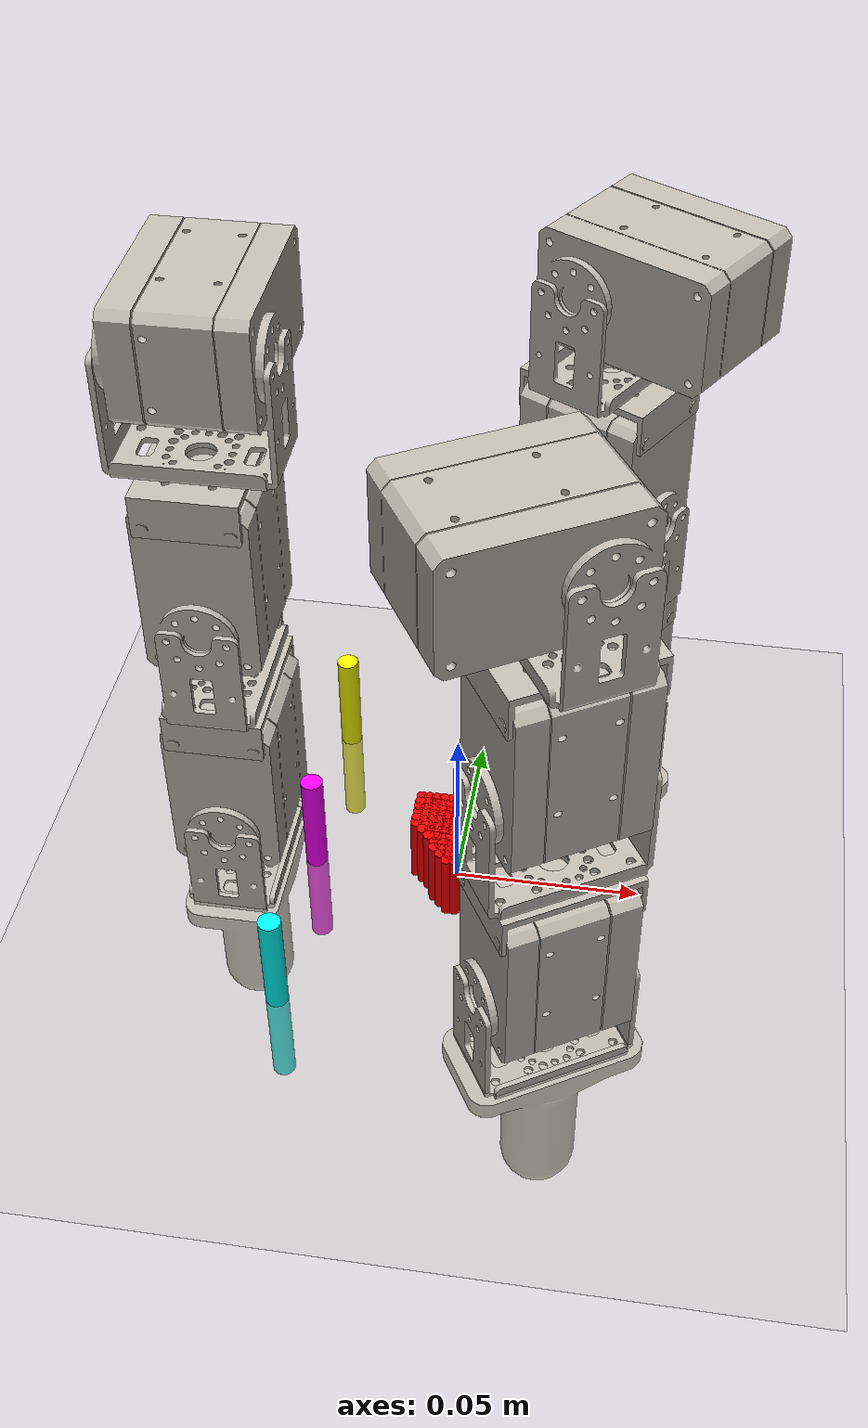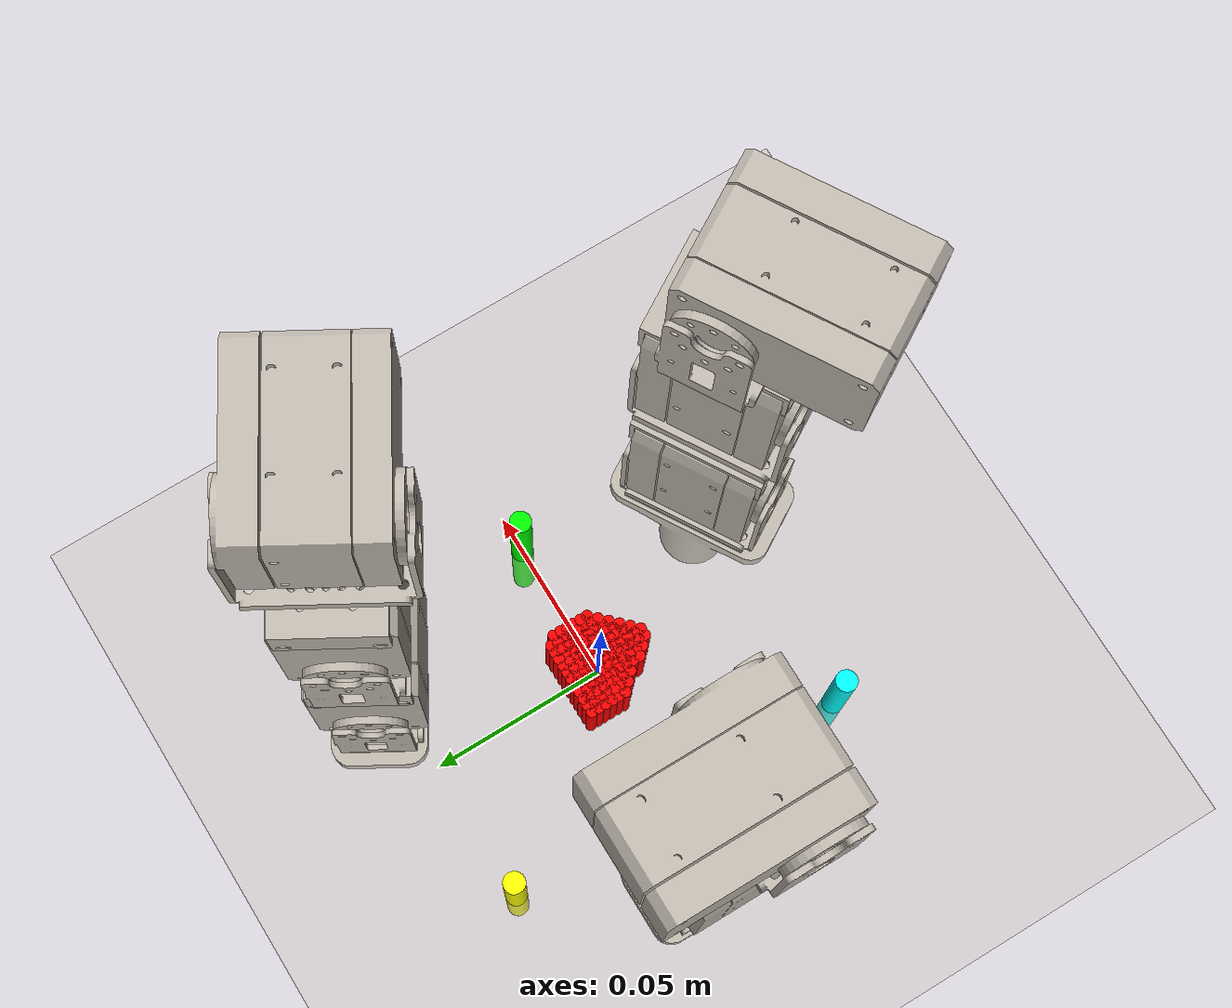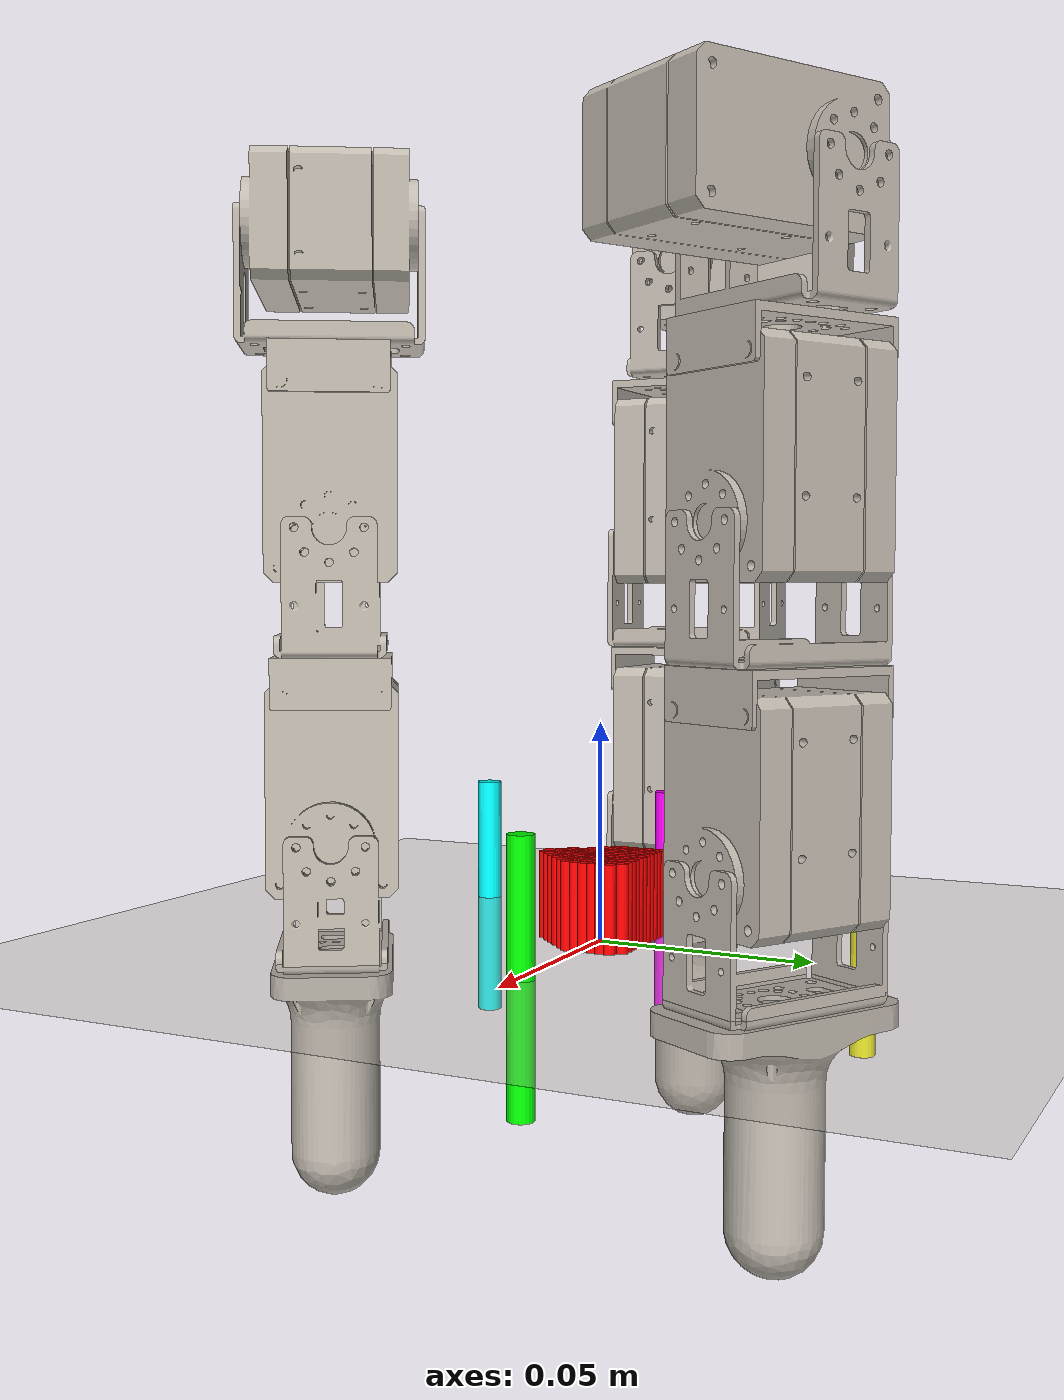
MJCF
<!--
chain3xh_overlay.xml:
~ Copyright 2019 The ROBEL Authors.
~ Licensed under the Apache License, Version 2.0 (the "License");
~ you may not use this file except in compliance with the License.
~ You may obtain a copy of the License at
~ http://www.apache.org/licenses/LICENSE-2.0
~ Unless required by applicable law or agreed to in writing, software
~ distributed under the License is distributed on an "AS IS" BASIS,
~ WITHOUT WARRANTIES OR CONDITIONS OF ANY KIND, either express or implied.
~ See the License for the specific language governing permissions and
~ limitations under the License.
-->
<?xml version="1.0"?>
<mujoco model="dclaw3xh_pushing">
  <include file="/scenes/scene_default.xml"/>
  <include file="/robot/assets/dependencies_3xh_position.xml"/>
  <include file="/pushing_object/dependencies_pushing_object.xml"/>

  <size njmax="8000" nconmax="4000"/>

  <worldbody>
    <camera name="canonical"            mode= "fixed" euler="0 0 1.5707963267948966" pos="0 0 0.192"/>
    <camera name="random"               mode= "fixed" euler="0 0 1.5707963267948966" pos="0 0 0.192"/>
    <camera name="canonical_nonfix"     mode= "fixed" euler="0 0 1.5707963267948966" pos="0 0 0.192"/>
    <camera name="random_nonfix"        mode= "fixed" euler="0 0 1.5707963267948966" pos="0 0 0.192"/>
    <camera name="canonical_overview"   mode= "fixed" euler="0 1 1.57" pos="0.3 0 0.4"/>
    <camera name="top"                  mode= "fixed" euler="0 0 1.57" pos="0 0 3"/>

    <body name="mount" pos="0 0 0.195" euler="0 0 0">
      <include file="./robot/assets/chain3xh_default.xml"/>
      <include file="./robot/assets/chain3xh_overlay.xml"/>
    </body>

    <body name="object1" pos="0 0 0">
      <include file="/pushing_object/object_current.xml"/>
    </body>

    <body name="init_mark" pos="0.04 0.0 0">
      <site type="cylinder" size=".003 .03" pos="0 0 0" rgba="0 1 0 1"/>
    </body>

    <!-- target -->
    <body name="target_left_mark" pos="-0.04 -0.05 0">
      <site name="target_left_mark" type="cylinder" size=".003 .03" pos="0 0 0" rgba="0 1 1 1"/>
    </body>

    <body name="target_center_mark" pos="-0.04 0.0 0">
      <site name="target_center_mark" type="cylinder" size=".003 .03" pos="0 0 0" rgba="1 0 1 1"/>
    </body>

    <body name="target_right_mark" pos="-0.04 0.05 0">
      <site name="target_right_mark" type="cylinder" size=".003 .03" pos="0 0 0" rgba="1 1 0 1"/>
    </body>

  </worldbody>
</mujoco>

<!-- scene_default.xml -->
<mujocoinclude>
  <asset>
    <texture name="skybox" type="skybox" builtin="gradient" rgb1=".08 .09 .10" rgb2="0 0 0" width="800" height="800" mark="random" markrgb=".8 .8 .8"/>

    <!-- Finger 1 -->
    <texture name="FFbase_xh28_tex"                type="2d" file="./pattern/pattern_default_crop.png" rgb1="1 1 1"/>
    <texture name="FF10_xh28_tex"                  type="2d" file="./pattern/pattern_default_crop.png" rgb1="1 1 1"/>
    <texture name="FF10_metal_clamping_tex"        type="2d" file="./pattern/pattern_default_crop.png" rgb1="1 1 1"/>
    <texture name="FF10_metal_clamping_small_tex"  type="2d" file="./pattern/pattern_default_crop.png" rgb1="1 1 1"/>
    <texture name="FFL11_xh28_tex"                 type="2d" file="./pattern/pattern_default_crop.png" rgb1="1 1 1"/>
    <texture name="FFL11_metal_clamping_tex"       type="2d" file="./pattern/pattern_default_crop.png" rgb1="1 1 1"/>
    <texture name="FFL11_metal_clamping_small_tex" type="2d" file="./pattern/pattern_default_crop.png" rgb1="1 1 1"/>
    <texture name="FFL11_plastic_finger_tex"       type="2d" file="./pattern/pattern_default_crop.png" rgb1="1 1 1"/>
    <texture name="FFL12_metal_clamping_tex"       type="2d" file="./pattern/pattern_default_crop.png" rgb1="1 1 1"/>
    <texture name="FFL12_plastic_finger_tex"       type="2d" file="./pattern/pattern_default_crop.png" rgb1="1 1 1"/>
    <texture name="FFL12_optoforce_sensor_tex"     type="2d" file="./pattern/pattern_default_crop.png" rgb1="1 1 1"/>
    <texture name="FFL12_optoforce_base_tex"       type="2d" file="./pattern/pattern_default_crop.png" rgb1="1 1 1"/>
    <material name="FFbase_xh28_mat"                shininess="0.03" specular="0.75" texture="FFbase_xh28_tex"></material>
    <material name="FF10_xh28_mat"                  shininess="0.03" specular="0.75" texture="FF10_xh28_tex"></material>
    <material name="FF10_metal_clamping_mat"        shininess="0.03" specular="0.75" texture="FF10_metal_clamping_tex"></material>
    <material name="FF10_metal_clamping_small_mat"  shininess="0.03" specular="0.75" texture="FF10_metal_clamping_small_tex"></material>
    <material name="FFL11_xh28_mat"                 shininess="0.03" specular="0.75" texture="FFL11_xh28_tex"></material>
    <material name="FFL11_metal_clamping_mat"       shininess="0.03" specular="0.75" texture="FFL11_metal_clamping_tex"></material>
    <material name="FFL11_metal_clamping_small_mat" shininess="0.03" specular="0.75" texture="FFL11_metal_clamping_small_tex"></material>
    <material name="FFL11_plastic_finger_mat"       shininess="0.03" specular="0.75" texture="FFL11_plastic_finger_tex"></material>
    <material name="FFL12_metal_clamping_mat"       shininess="0.03" specular="0.75" texture="FFL12_metal_clamping_tex"></material>
    <material name="FFL12_plastic_finger_mat"       shininess="0.03" specular="0.75" texture="FFL12_plastic_finger_tex"></material>
    <material name="FFL12_optoforce_sensor_mat"     shininess="0.03" specular="0.75" texture="FFL12_optoforce_sensor_tex"></material>
    <material name="FFL12_optoforce_base_mat"       shininess="0.03" specular="0.75" texture="FFL12_optoforce_base_tex"></material>

    <!-- Finger 2 -->
    <texture name="MFbase_xh28_tex"                type="2d" file="./pattern/pattern_default_crop.png" rgb1="1 1 1"/>
    <texture name="MF20_xh28_tex"                  type="2d" file="./pattern/pattern_default_crop.png" rgb1="1 1 1"/>
    <texture name="MF20_metal_clamping_tex"        type="2d" file="./pattern/pattern_default_crop.png" rgb1="1 1 1"/>
    <texture name="MF20_metal_clamping_small_tex"  type="2d" file="./pattern/pattern_default_crop.png" rgb1="1 1 1"/>
    <texture name="MFL21_xh28_tex"                 type="2d" file="./pattern/pattern_default_crop.png" rgb1="1 1 1"/>
    <texture name="MFL21_metal_clamping_tex"       type="2d" file="./pattern/pattern_default_crop.png" rgb1="1 1 1"/>
    <texture name="MFL21_metal_clamping_small_tex" type="2d" file="./pattern/pattern_default_crop.png" rgb1="1 1 1"/>
    <texture name="MFL21_plastic_finger_tex"       type="2d" file="./pattern/pattern_default_crop.png" rgb1="1 1 1"/>
    <texture name="MFL22_metal_clamping_tex"       type="2d" file="./pattern/pattern_default_crop.png" rgb1="1 1 1"/>
    <texture name="MFL22_plastic_finger_tex"       type="2d" file="./pattern/pattern_default_crop.png" rgb1="1 1 1"/>
    <texture name="MFL22_optoforce_sensor_tex"     type="2d" file="./pattern/pattern_default_crop.png" rgb1="1 1 1"/>
    <texture name="MFL22_optoforce_base_tex"       type="2d" file="./pattern/pattern_default_crop.png" rgb1="1 1 1"/>
    <material name="MFbase_xh28_mat"                shininess="0.03" specular="0.75" texture="MFbase_xh28_tex"></material>
    <material name="MF20_xh28_mat"                  shininess="0.03" specular="0.75" texture="MF20_xh28_tex"></material>
    <material name="MF20_metal_clamping_mat"        shininess="0.03" specular="0.75" texture="MF20_metal_clamping_tex"></material>
    <material name="MF20_metal_clamping_small_mat"  shininess="0.03" specular="0.75" texture="MF20_metal_clamping_small_tex"></material>
    <material name="MFL21_xh28_mat"                 shininess="0.03" specular="0.75" texture="MFL21_xh28_tex"></material>
    <material name="MFL21_metal_clamping_mat"       shininess="0.03" specular="0.75" texture="MFL21_metal_clamping_tex"></material>
    <material name="MFL21_metal_clamping_small_mat" shininess="0.03" specular="0.75" texture="MFL21_metal_clamping_small_tex"></material>
    <material name="MFL21_plastic_finger_mat"       shininess="0.03" specular="0.75" texture="MFL21_plastic_finger_tex"></material>
    <material name="MFL22_metal_clamping_mat"       shininess="0.03" specular="0.75" texture="MFL22_metal_clamping_tex"></material>
    <material name="MFL22_plastic_finger_mat"       shininess="0.03" specular="0.75" texture="MFL22_plastic_finger_tex"></material>
    <material name="MFL22_optoforce_sensor_mat"     shininess="0.03" specular="0.75" texture="MFL22_optoforce_sensor_tex"></material>
    <material name="MFL22_optoforce_base_mat"       shininess="0.03" specular="0.75" texture="MFL22_optoforce_base_tex"></material>

    <!-- Finger 3 -->
    <texture name="THbase_xh28_tex"                type="2d" file="./pattern/pattern_default_crop.png" rgb1="1 1 1"/>
    <texture name="TH30_xh28_tex"                  type="2d" file="./pattern/pattern_default_crop.png" rgb1="1 1 1"/>
    <texture name="TH30_metal_clamping_tex"        type="2d" file="./pattern/pattern_default_crop.png" rgb1="1 1 1"/>
    <texture name="TH30_metal_clamping_small_tex"  type="2d" file="./pattern/pattern_default_crop.png" rgb1="1 1 1"/>
    <texture name="THL31_xh28_tex"                 type="2d" file="./pattern/pattern_default_crop.png" rgb1="1 1 1"/>
    <texture name="THL31_metal_clamping_tex"       type="2d" file="./pattern/pattern_default_crop.png" rgb1="1 1 1"/>
    <texture name="THL31_metal_clamping_small_tex" type="2d" file="./pattern/pattern_default_crop.png" rgb1="1 1 1"/>
    <texture name="THL31_plastic_finger_tex"       type="2d" file="./pattern/pattern_default_crop.png" rgb1="1 1 1"/>
    <texture name="THL32_metal_clamping_tex"       type="2d" file="./pattern/pattern_default_crop.png" rgb1="1 1 1"/>
    <texture name="THL32_plastic_finger_tex"       type="2d" file="./pattern/pattern_default_crop.png" rgb1="1 1 1"/>
    <texture name="THL32_optoforce_sensor_tex"     type="2d" file="./pattern/pattern_default_crop.png" rgb1="1 1 1"/>
    <texture name="THL32_optoforce_base_tex"       type="2d" file="./pattern/pattern_default_crop.png" rgb1="1 1 1"/>
    <material name="THbase_xh28_mat"                shininess="0.03" specular="0.75" texture="THbase_xh28_tex"></material>
    <material name="TH30_xh28_mat"                  shininess="0.03" specular="0.75" texture="TH30_xh28_tex"></material>
    <material name="TH30_metal_clamping_mat"        shininess="0.03" specular="0.75" texture="TH30_metal_clamping_tex"></material>
    <material name="TH30_metal_clamping_small_mat"  shininess="0.03" specular="0.75" texture="TH30_metal_clamping_small_tex"></material>
    <material name="THL31_xh28_mat"                 shininess="0.03" specular="0.75" texture="THL31_xh28_tex"></material>
    <material name="THL31_metal_clamping_mat"       shininess="0.03" specular="0.75" texture="THL31_metal_clamping_tex"></material>
    <material name="THL31_metal_clamping_small_mat" shininess="0.03" specular="0.75" texture="THL31_metal_clamping_small_tex"></material>
    <material name="THL31_plastic_finger_mat"       shininess="0.03" specular="0.75" texture="THL31_plastic_finger_tex"></material>
    <material name="THL32_metal_clamping_mat"       shininess="0.03" specular="0.75" texture="THL32_metal_clamping_tex"></material>
    <material name="THL32_plastic_finger_mat"       shininess="0.03" specular="0.75" texture="THL32_plastic_finger_tex"></material>
    <material name="THL32_optoforce_sensor_mat"     shininess="0.03" specular="0.75" texture="THL32_optoforce_sensor_tex"></material>
    <material name="THL32_optoforce_base_mat"       shininess="0.03" specular="0.75" texture="THL32_optoforce_base_tex"></material>

    <!-- xh28 -->
    <texture name="xh28_tex" type="2d" file="./pattern/pattern_default_crop.png" rgb1="1 1 1"/>
    <material name="xh28_mat" shininess="0.03" specular="0.75" texture="xh28_tex"></material>

    <!-- acrylic_circle -->
    <texture name="acrylic_circle_tex" type="2d" file="./pattern/pattern_default_crop.png" rgb1="1 1 1"/>
    <material name="acrylic_circle_mat" shininess="0.03" specular="0.75" texture="acrylic_circle_tex"></material>

    <!-- floor -->
    <texture name="floor_tex" type="2d" file="./pattern/pattern_default_crop.png" rgb1="1 1 1"/>
    <material name="floor_mat" shininess="0.03" specular="0.75" texture="floor_tex"></material>

    <!-- mount -->
    <texture name="mount_tex" type="2d" file="./pattern/pattern_default_crop.png" rgb1="1 1 1"/>
    <material name="mount_mat" shininess="0.03" specular="0.75" texture="mount_tex"></material>

    <!-- valve_3 -->
    <texture name="valve_3_tex" type="2d" file="./pattern/pattern_default_crop.png" rgb1="1 1 1"/>
    <material name="valve_3_mat" shininess="0.03" specular="0.75" texture="valve_3_tex"></material>

    <!-- valve_3 individual -->
    <texture name="valve_3fin_handle_1_tex" type="2d" file="./pattern/pattern_default_crop.png" rgb1="1 1 1"/>
    <texture name="valve_3fin_handle_2_tex" type="2d" file="./pattern/pattern_default_crop.png" rgb1="1 1 1"/>
    <texture name="valve_3fin_handle_3_tex" type="2d" file="./pattern/pattern_default_crop.png" rgb1="1 1 1"/>
    <texture name="valve_3fin_center_tex"   type="2d" file="./pattern/pattern_default_crop.png" rgb1="1 1 1"/>
    <material name="valve_3fin_handle_1_mat" shininess="0.03" specular="0.75" texture="valve_3fin_handle_1_tex"></material>
    <material name="valve_3fin_handle_2_mat" shininess="0.03" specular="0.75" texture="valve_3fin_handle_2_tex"></material>
    <material name="valve_3fin_handle_3_mat" shininess="0.03" specular="0.75" texture="valve_3fin_handle_3_tex"></material>
    <material name="valve_3fin_center_mat"   shininess="0.03" specular="0.75" texture="valve_3fin_center_tex"></material>

  </asset>

  <visual>
    <quality shadowsize="1024" offsamples="4"/>
  </visual>

  <worldbody>

    <light name="light_top_1" directional="true" diffuse=".3 .3 .3" specular="0.3 0.3 0.3" pos="-0.5 -0.5 1.0" active="false" dir="0.5 0.5 -1"/>
    <light name="light_top_2" directional="true" diffuse=".3 .3 .3" specular="0.3 0.3 0.3" pos="0.0 -0.5 1.0"  active="false" dir="0.0 0.5 -1"/>
    <light name="light_top_3" directional="true" diffuse=".3 .3 .3" specular="0.3 0.3 0.3" pos="0.5 -0.5 1.0"  active="true" dir="-0.5 0.5 -1"/>
    <light name="light_top_4" directional="true" diffuse=".3 .3 .3" specular="0.3 0.3 0.3" pos="-0.5 0.0 1.0"  active="false" dir="0.5 0 -1"/>
    <light name="light_top_5" directional="true" diffuse=".3 .3 .3" specular="0.3 0.3 0.3" pos="0.0 0.0 1.0"   active="false" dir="0 0 -1"/>
    <light name="light_top_6" directional="true" diffuse=".3 .3 .3" specular="0.3 0.3 0.3" pos="0.5 0.0 1.0"   active="false" dir="-0.5 0 -1"/>
    <light name="light_top_7" directional="true" diffuse=".3 .3 .3" specular="0.3 0.3 0.3" pos="-0.5 0.5 1.0"  active="true" dir=" 0.5 -0.5 -1"/>
    <light name="light_top_8" directional="true" diffuse=".3 .3 .3" specular="0.3 0.3 0.3" pos="0.0 0.5 1.0"   active="false" dir=" 0.0 -0.5 -1"/>
    <light name="light_top_9" directional="true" diffuse=".3 .3 .3" specular="0.3 0.3 0.3" pos="0.5 0.5 1.0"   active="false" dir="-0.5 -0.5 -1"/>

    <light name="light_side_1" directional="true" diffuse=".3 .3 .3" specular="0.3 0.3 0.3" pos="0.0 0.5 0.2"   active="false" dir=" 0.0 -0.5 0.0"/>
    <light name="light_side_2" directional="true" diffuse=".3 .3 .3" specular="0.3 0.3 0.3" pos="0.0 -0.5 0.2"  active="false" dir=" 0.0 0.5 0.0"/>
    <light name="light_side_3" directional="true" diffuse=".3 .3 .3" specular="0.3 0.3 0.3" pos="0.5 0.0 0.2"   active="false" dir="-0.5 0.0 0.0"/>
    <light name="light_side_4" directional="true" diffuse=".3 .3 .3" specular="0.3 0.3 0.3" pos="-0.5 0.0 0.2"  active="false" dir=" 0.5 0.0 0.0"/>
    <light name="light_side_5" directional="true" diffuse=".3 .3 .3" specular="0.3 0.3 0.3" pos="-0.5 0.5 0.2"  active="false" dir=" 0.5 -0.5 0.0"/>
    <light name="light_side_6" directional="true" diffuse=".3 .3 .3" specular="0.3 0.3 0.3" pos=" 0.5 -0.5 0.2" active="false" dir="-0.5 0.5 0.0"/>
    <light name="light_side_7" directional="true" diffuse=".3 .3 .3" specular="0.3 0.3 0.3" pos="-0.5 -0.5 0.2" active="false" dir=" 0.5 0.5 0.0"/>
    <light name="light_side_8" directional="true" diffuse=".3 .3 .3" specular="0.3 0.3 0.3" pos=" 0.5  0.5 0.2" active="false" dir="-0.5 -0.5 0.0"/>

    <geom name="floor" pos="0 0 0"  size="5 5 .1"       conaffinity="1" contype="1" type="plane" condim="3" material="floor_mat" />
    <site name="xaxis" pos=".5 0 0" size=".005 .5" type="capsule" rgba="1 0 0 .25" euler="0 1.57 0" group="3"/>
    <site name="yaxis" pos="0 .5 0" size=".005 .5" type="capsule" rgba="0 1 0 .25" euler="1.57 0 0" group="3"/>
  </worldbody>
</mujocoinclude>

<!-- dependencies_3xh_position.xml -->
<mujocoinclude>
  <compiler angle="radian" inertiafromgeom="auto" inertiagrouprange="3 5" />
  <option timestep="0.0025" iterations="50" tolerance="1e-10" solver="Newton" jacobian="dense" cone="elliptic"/>
  <asset>
    <mesh name="xh28"                 file="./robot/meshes/xh_base_high_poly.stl"            scale=".001 .001 .001"/>
    <mesh name="acrylic_circle"       file="./robot/meshes/acrylic_circle.stl"               scale=".1 .1 .1"/>
    <mesh name="plastic_finger"       file="./robot/meshes/xh_finger_tip.stl"                scale=".001 .001 .001"/>
    <mesh name="metal_clamping"       file="./robot/meshes/xh_clamping_high_poly.stl"        scale=".001 .001 .001"/>
    <mesh name="metal_clamping_small" file="./robot/meshes/xh_clamping_small_high_poly.stl"  scale=".001 .001 .001"/>
    <mesh name="plastic_top"          file="./robot/meshes/xh_white_top_high_poly.stl"       scale=".001 .001 .001"/>
    <mesh name="xh28_hull"            file="./robot/meshes/xh_base_hull.stl"                 scale=".001 .001 .001"/>
    <mesh name="xh28_hull_top"        file="./robot/meshes/xh_base_hull_top.stl"             scale=".001 .001 .001"/>
  </asset>
  <default>
    <default class="dclaw3xh">
      <joint limited="true" damping=".1" armature="0.001"/>
      <geom contype="0"   conaffinity="0" condim="4" group="1" margin="0.0005" material="metal_black" type="mesh"/>
      <motor ctrlrange="-1.57 1.57" ctrllimited="true"/>
      <site group="1"/>
      <default class="overlay">
        <geom contype="0" conaffinity="0" group="3" type="mesh" material="greenish"/>
        <joint damping="100" frictionloss="100" armature="0"/>
        <site group="3"/>
      </default>
      <default class="phy_metal">
        <geom contype="1" conaffinity="1" group="4" type="mesh" rgba="0.0 0.0 1.0 .3"/>
        <site group="4"/>
      </default>
      <default class="phy_plastic">
        <geom contype="1" conaffinity="1" group="4" type="mesh" rgba="0.0 0.0 1.0 .3" friction=".2 0.005 0.0001"/>
        <site group="4"/>
      </default>
    </default>
  </default>
  <asset>
    <material name="metal_black" specular="1" shininess="1" rgba="0.2 0.2 0.2 1.0"/>
    <material name="metal_grey" specular="1" shininess="1" rgba="0.5 0.5 0.5 1.0"/>
    <material name="plastic" specular="0.3" shininess="0" rgba="1 1 1 1"/>
    <material name="acrylic" specular="0.3" shininess="0" rgba="1 1 1 .2"/>
    <material name="greenish" specular="0.0" shininess="0" rgba="0.3 1 0.3 1"/>
  </asset>

  <actuator>
    <position name="FFJ10_pos_sensor" kp="2" joint="FFJ10" class="dclaw3xh"  />
    <position name="FFJ11_pos_sensor" kp="2" joint="FFJ11" class="dclaw3xh"  />
    <position name="FFJ12_pos_sensor" kp="2" joint="FFJ12" class="dclaw3xh"  />
    <position name="MFJ20_pos_sensor" kp="2" joint="MFJ20" class="dclaw3xh"  />
    <position name="MFJ21_pos_sensor" kp="2" joint="MFJ21" class="dclaw3xh"  />
    <position name="MFJ22_pos_sensor" kp="2" joint="MFJ22" class="dclaw3xh"  />
    <position name="THJ30_pos_sensor" kp="2" joint="THJ30" class="dclaw3xh"  />
    <position name="THJ31_pos_sensor" kp="2" joint="THJ31" class="dclaw3xh"  />
    <position name="THJ32_pos_sensor" kp="2" joint="THJ32" class="dclaw3xh"  />
  </actuator>

</mujocoinclude>

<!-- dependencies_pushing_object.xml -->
<mujocoinclude>
  <compiler angle="radian" inertiafromgeom="auto" inertiagrouprange="3 5"/>
  <option timestep="0.0025"/>
  <asset>
    <!-- texture -->
    <texture name="object_tex" type="2d" file="./pattern/pattern_default_crop.png" rgb1="1 1 1"/>
    <!-- material -->
    <material name="object_mat" shininess="0.03" specular="0.75" texture="object_tex"/>
  </asset>

  <default>
    <default class="pushing_object">
      <joint limited="true" damping=".1" armature="0.001"/>
      <geom contype="1" conaffinity="1" condim="4" group="2" margin="0.0005"/>
      <site group="2"/>

      <default class="pushing_object_viz">
        <geom contype="0" conaffinity="0" material="object_mat"/>
      </default>

      <default class="pushing_object_phy">
        <geom contype="1" conaffinity="1" group="4" type="mesh" rgba="0.0 0.0 1.0 .3" friction=".2 0.005 0.0001"/>
        <site group="4"/>
      </default>

    </default>
  </default>

</mujocoinclude>

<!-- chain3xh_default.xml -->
<mujocoinclude>
  <body name="dClaw" euler="3.14 0 0" childclass="dclaw3xh">
    <geom class="phy_metal" type="cylinder" size="0.075 0.004" mass=".11" />
    <site name="S_grasp" pos="0 0 0.24" type="sphere" size="0.01" group="4"/>
    <!-- INDEX/FIRST FINGER -->
    <body name="FFbase" pos=".03 -0.052 .020" euler="0 0 .52">
      <geom name="FFbase_xh28" mesh="xh28" pos="0 0 0.01425" euler="1.57 0 1.57" material="FFbase_xh28_mat"/>
      <geom class="phy_metal" type="box" pos=".012 0 0.014" size="0.024 0.0175 0.015" mass=".093" />
      <body name="FF10" pos="0 0 0.01425" euler="0 0 3.14">
        <geom name="FF10_metal_clamping"        mesh="metal_clamping"                       euler="0 0 1.57"    material="FF10_metal_clamping_mat"/>
        <geom name="FF10_metal_clamping_small"  mesh="metal_clamping_small" pos="0 0 0.055" euler="3.14 0 0"    material="FF10_metal_clamping_small_mat"/>
        <geom name="FF10_xh28"                  mesh="xh28"                 pos="0 0 0.068" euler="1.57 1.57 0" material="FF10_xh28_mat"/>
        <geom class="phy_metal" type="box" pos="0 0 0.056" size="0.0175 0.015 0.024" mass=".093"     />
        <geom class="phy_metal" type="box" pos="0.0 0 0.026" size="0.0125 0.0214 0.003" mass=".003"  />
        <geom class="phy_metal" type="box" pos="0 0.02 0.013" size="0.011 0.0012 0.016" mass=".002"  />
        <geom class="phy_metal" type="box" pos="0 -0.02 0.013" size="0.011 0.0012 0.016" mass=".002" />
        <geom class="phy_metal" type="box" pos="0 0 0.033" size="0.019 0.014 0.006" mass=".005"      />
        <joint name="FFJ10" type="hinge" axis="0 1 0" range="-1.57 1.57"/>
        <body name="FFL11" pos="0 0 0.0675">
          <geom name="FFL11_metal_clamping_small" mesh="metal_clamping_small" pos="0 0 0.055"   euler="3.14 0 0"    material="FFL11_metal_clamping_small_mat"/>
          <geom name="FFL11_xh28"                 mesh="xh28"                 pos="0 0 0.0686"  euler="1.57 1.57 0" material="FFL11_xh28_mat"/>
          <geom name="FFL11_metal_clamping"       mesh="metal_clamping"                                             material="FFL11_metal_clamping_mat"/>
          <geom class="phy_metal" type="box" pos="0 0 0.056" size="0.0175 0.015 0.024" mass=".093"     />
          <geom class="phy_metal" type="box" pos="0 0 0.026" size="0.0214 0.0125 0.003" mass=".003"    />
          <geom class="phy_metal" type="box" pos="0.02 0 0.013" size="0.0012 0.011 0.016" mass=".002"  />
          <geom class="phy_metal" type="box" pos="-0.02 0 0.013" size="0.0012 0.011 0.016" mass=".002" />
          <geom class="phy_metal" type="box" pos="0 0 0.033" size="0.019 0.014 0.006" mass=".005"      />
          <joint name="FFJ11" type="hinge" axis="1 0 0" range="-1.57 1.57"/>
          <body name="FFL12" pos="0 0 0.068">
            <geom name="FFL12_metal_clamping" mesh="metal_clamping"                 material="FFL12_metal_clamping_mat"/>
            <geom name="FFL12_plastic_finger" mesh="plastic_finger" pos="0 0 0.046" material="FFL12_plastic_finger_mat"/>
            <geom class="phy_metal" type="box" pos="0.0 0 0.026" size="0.0214 0.0125 0.003" mass=".003" />
            <geom class="phy_metal" type="box" pos="0.02 0 0.013" size="0.0012 0.011 0.016" mass=".002" />
            <geom class="phy_metal" type="box" pos="-0.02 0 0.013" size="0.0012 0.011 0.016" mass=".002"/>
            <geom class="phy_plastic" type="capsule" pos="-0.00008 0.00003 0.0529"  size="0.0101 0.0195"       mass=".018"/>
            <geom class="phy_plastic" type="box"     pos="0 0 0.03"                 size="0.0241 0.0131 0.003"  mass=".007"/>
            <joint name="FFJ12" type="hinge" axis="1 0 0" range="-1.57 1.57"/>
          </body>
        </body>
      </body>
    </body>
    <!-- MIDDLE FINGER -->
    <body name="MFbase" pos=".03 0.052 .020" euler="0 0 2.6">
      <geom name="MFbase_xh28" mesh="xh28" pos="0 0 0.01425" euler="1.57 0 1.57"  material="MFbase_xh28_mat"/>
      <geom class="phy_metal" type="box" pos=".012 0 0.014" size="0.024 0.0175 0.015" mass=".093" />
      <body name="MF20" pos="0 0 0.01425" euler="0 0 3.14">
        <geom name="MF20_metal_clamping"        mesh="metal_clamping"                       euler="0 0 1.57"    material="MF20_metal_clamping_mat"/>
        <geom name="MF20_metal_clamping_small"  mesh="metal_clamping_small" pos="0 0 0.055" euler="3.14 0 0"    material="MF20_metal_clamping_small_mat"/>
        <geom name="MF20_xh28"                  mesh="xh28"                 pos="0 0 0.068" euler="1.57 1.57 0" material="MF20_xh28_mat"/>
        <geom class="phy_metal" type="box" pos="0 0 0.056" size="0.0175 0.015 0.024" mass=".093"     />
        <geom class="phy_metal" type="box" pos="0.0 0 0.026" size="0.0125 0.0214 0.003" mass=".003"  />
        <geom class="phy_metal" type="box" pos="0 0.02 0.013" size="0.011 0.0012 0.016" mass=".002"  />
        <geom class="phy_metal" type="box" pos="0 -0.02 0.013" size="0.011 0.0012 0.016" mass=".002" />
        <geom class="phy_metal" type="box" pos="0 0 0.033" size="0.019 0.014 0.006" mass=".005"      />
        <joint name="MFJ20" type="hinge" axis="0 1 0" range="-1.57 1.57"/>
        <body name="MFL21" pos="0 0 0.0675">
          <geom name="MFL21_metal_clamping_small" mesh="metal_clamping_small" pos="0 0 0.055"   euler="3.14 0 0"    material="MFL21_metal_clamping_small_mat"/>
          <geom name="MFL21_xh28"                 mesh="xh28"                 pos="0 0 0.0686"  euler="1.57 1.57 0" material="MFL21_xh28_mat"/>
          <geom name="MFL21_metal_clamping"       mesh="metal_clamping"                                             material="MFL21_metal_clamping_mat"/>
          <geom class="phy_metal" type="box" pos="0 0 0.056" size="0.0175 0.015 0.024" mass=".093"     />
          <geom class="phy_metal" type="box" pos="0 0 0.026" size="0.0214 0.0125 0.003" mass=".003"    />
          <geom class="phy_metal" type="box" pos="0.02 0 0.013" size="0.0012 0.011 0.016" mass=".002"  />
          <geom class="phy_metal" type="box" pos="-0.02 0 0.013" size="0.0012 0.011 0.016" mass=".002" />
          <geom class="phy_metal" type="box" pos="0 0 0.033" size="0.019 0.014 0.006" mass=".005"      />
          <joint name="MFJ21" type="hinge" axis="1 0 0" range="-1.57 1.57"/>
          <body name="MFL22" pos="0 0 0.068">
            <geom name="MFL22_metal_clamping" mesh="metal_clamping"                 material="MFL22_metal_clamping_mat"/>
            <geom name="MFL22_plastic_finger" mesh="plastic_finger" pos="0 0 0.046" material="MFL22_plastic_finger_mat"/>
            <geom class="phy_metal" type="box" pos="0.0 0 0.026" size="0.0214 0.0125 0.003" mass=".003" />
            <geom class="phy_metal" type="box" pos="0.02 0 0.013" size="0.0012 0.011 0.016" mass=".002" />
            <geom class="phy_metal" type="box" pos="-0.02 0 0.013" size="0.0012 0.011 0.016" mass=".002"/>
            <geom class="phy_plastic" type="capsule" pos="-0.00008 0.00003 0.0529"  size="0.0101 0.0195"       mass=".018"/>
            <geom class="phy_plastic" type="box"     pos="0 0 0.03"                 size="0.0241 0.0131 0.003"  mass=".007"/>
            <joint name="MFJ22" type="hinge" axis="1 0 0" range="-1.57 1.57"/>
          </body>
        </body>
      </body>
    </body>
    <!-- THUMB -->
    <body name="THbase" pos="-.06 0 .020" euler="0 0 -1.57">
      <geom name="THbase_xh28" mesh="xh28" pos="0 0 0.01425" euler="1.57 0 1.57" material="THbase_xh28_mat"/>
      <geom class="phy_metal" type="box" pos=".012 0 0.014" size="0.024 0.0175 0.015" mass=".093" />
      <body name="TH30" pos="0 0 0.01425" euler="0 0 3.14">
        <geom name="TH30_metal_clamping"        mesh="metal_clamping"                       euler="0 0 1.57"    material="TH30_metal_clamping_mat"/>
        <geom name="TH30_metal_clamping_small"  mesh="metal_clamping_small" pos="0 0 0.055" euler="3.14 0 0"    material="TH30_metal_clamping_small_mat"/>
        <geom name="TH30_xh28"                  mesh="xh28"                 pos="0 0 0.068" euler="1.57 1.57 0" material="TH30_xh28_mat"/>
        <geom class="phy_metal" type="box" pos="0 0 0.056" size="0.0175 0.015 0.024" mass=".093"     />
        <geom class="phy_metal" type="box" pos="0.0 0 0.026" size="0.0125 0.0214 0.003" mass=".003"  />
        <geom class="phy_metal" type="box" pos="0 0.02 0.013" size="0.011 0.0012 0.016" mass=".002"  />
        <geom class="phy_metal" type="box" pos="0 -0.02 0.013" size="0.011 0.0012 0.016" mass=".002" />
        <geom class="phy_metal" type="box" pos="0 0 0.033" size="0.019 0.014 0.006" mass=".005"      />
        <joint name="THJ30" type="hinge" axis="0 1 0" range="-1.57 1.57"/>
        <body name="THL31" pos="0 0 0.0675">
          <geom name="THL31_metal_clamping_small" mesh="metal_clamping_small" pos="0 0 0.055"   euler="3.14 0 0"    material="THL31_metal_clamping_small_mat"/>
          <geom name="THL31_xh28"                 mesh="xh28"                 pos="0 0 0.0686"  euler="1.57 1.57 0" material="THL31_xh28_mat"/>
          <geom name="THL31_metal_clamping"       mesh="metal_clamping"                                             material="THL31_metal_clamping_mat"/>
          <geom class="phy_metal" type="box" pos="0 0 0.056" size="0.0175 0.015 0.024" mass=".093"    />
          <geom class="phy_metal" type="box" pos="0 0 0.026" size="0.0214 0.0125 0.003" mass=".003"   />
          <geom class="phy_metal" type="box" pos="0.02 0 0.013" size="0.0012 0.011 0.016" mass=".002" />
          <geom class="phy_metal" type="box" pos="-0.02 0 0.013" size="0.0012 0.011 0.016" mass=".002"/>
          <geom class="phy_metal" type="box" pos="0 0 0.033" size="0.019 0.014 0.006" mass=".005"     />
          <joint name="THJ31" type="hinge" axis="1 0 0" range="-1.57 1.57"/>
          <body name="THL32" pos="0 0 0.068">
            <geom name="THL32_metal_clamping" mesh="metal_clamping"                 material="THL32_metal_clamping_mat"/>
            <geom name="THL32_plastic_finger" mesh="plastic_finger" pos="0 0 0.046" material="THL32_plastic_finger_mat"/>
            <geom class="phy_metal"   type="box"     pos="0.0 0 0.026"    size="0.0214 0.0125 0.003" mass=".003"/>
            <geom class="phy_metal"   type="box"     pos="0.02 0 0.013"   size="0.0012 0.011 0.016"  mass=".002"/>
            <geom class="phy_metal"   type="box"     pos="-0.02 0 0.013"  size="0.0012 0.011 0.016"  mass=".002"/>
            <geom class="phy_plastic" type="capsule" pos="-0.00008 0.00003 0.0529"  size="0.0101 0.0195"       mass=".018"/>
            <geom class="phy_plastic" type="box"     pos="0 0 0.03"                 size="0.0241 0.0131 0.003"  mass=".007"/>
            <joint name="THJ32" type="hinge" axis="1 0 0" range="-1.57 1.57"/>
          </body>
        </body>
      </body>
    </body>
  </body>
</mujocoinclude>

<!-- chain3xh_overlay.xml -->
<mujocoinclude>
  <body name="_dclaw" euler="3.14 0 0" childclass="overlay">
    <geom mesh="acrylic_circle"/>
    <!-- INDEX/FIRST FINGER -->
    <body name="_FFbase" pos=".03 -0.052 .003" euler="0 0 .52">
      <geom mesh="xh28" pos="0 0 0.01425" euler="1.57 0 1.57"/>
      <body name="_FF10" pos="0 0 0.01425" euler="0 0 3.14">
        <geom mesh="metal_clamping" euler="0 0 1.57"/>
        <geom mesh="metal_clamping_small" pos="0 0 0.055" euler="3.14 0 0"/>
        <geom mesh="xh28" pos="0 0 0.068" euler="1.57 1.57 0"/>
        <joint name="_FFJ10" type="hinge" axis="0 1 0" range="-.45 1.35"/>
        <body name="_FFL11" pos="0 0 0.0675">
          <geom mesh="metal_clamping_small" pos="0 0 0.055" euler="3.14 0 0"/>
          <geom mesh="xh28" pos="0 0 0.0686" euler="1.57 1.57 0"/>
          <geom mesh="metal_clamping"/>
          <joint name="_FFJ11" type="hinge" axis="1 0 0" range="-2 2"/>
          <body name="_FFL12" pos="0 0 0.068">
            <geom mesh="metal_clamping"/>
            <geom mesh="plastic_finger" pos="0 0 0.046"/>
            <joint name="_FFJ12" type="hinge" axis="1 0 0" range="-2 2"/>
            <site name="_FFtip" type="sphere" pos="0 0 .076" size="0.01" rgba="1 .3 .3 1"/>
          </body>
        </body>
      </body>
    </body>
    <!-- MIDDLE FINGER -->
    <body name="_MFbase" pos=".03 0.052 .003" euler="0 0 2.62">
      <geom mesh="xh28" pos="0 0 0.01425" euler="1.57 0 1.57"/>
      <body name="_MF20" pos="0 0 0.01425" euler="0 0 3.14">
        <geom mesh="metal_clamping" euler="0 0 1.57"/>
        <geom mesh="metal_clamping_small" pos="0 0 0.055" euler="3.14 0 0"/>
        <geom mesh="xh28" pos="0 0 0.068" euler="1.57 1.57 0"/>
        <joint name="_MFJ20" type="hinge" axis="0 1 0" range="-.45 1.35"/>
        <body name="_MFL21" pos="0 0 0.0675">
          <geom mesh="metal_clamping_small" pos="0 0 0.055" euler="3.14 0 0"/>
          <geom mesh="xh28" pos="0 0 0.0686" euler="1.57 1.57 0"/>
          <geom mesh="metal_clamping"/>
          <joint name="_MFJ21" type="hinge" axis="1 0 0" range="-2 2"/>
          <body name="_MFL22" pos="0 0 0.068">
            <geom mesh="metal_clamping"/>
            <geom mesh="plastic_finger" pos="0 0 0.046"/>
            <joint name="_MFJ22" type="hinge" axis="1 0 0" range="-2 2"/>
            <site name="_MFtip" type="sphere" pos="0 0 .076" size="0.01" rgba=".3 1 .3 1"/>
          </body>
        </body>
      </body>
    </body>
    <!-- THUMB -->
    <body name="_THbase" pos="-.06 0 .003" euler="0 0 -1.57">
      <geom mesh="xh28" pos="0 0 0.01425" euler="1.57 0 1.57"/>
      <body name="_TH30" pos="0 0 0.01425" euler="0 0 3.14">
        <geom mesh="metal_clamping" euler="0 0 1.57"/>
        <geom mesh="metal_clamping_small" pos="0 0 0.055" euler="3.14 0 0"/>
        <geom mesh="xh28" pos="0 0 0.068" euler="1.57 1.57 0"/>
        <joint name="_THJ30" type="hinge" axis="0 1 0" range="-.45 1.35"/>
        <body name="_THL31" pos="0 0 0.0675">
          <geom mesh="metal_clamping_small" pos="0 0 0.055" euler="3.14 0 0"/>
          <geom mesh="xh28" pos="0 0 0.0686" euler="1.57 1.57 0"/>
          <geom mesh="metal_clamping"/>
          <joint name="_THJ31" type="hinge" axis="1 0 0" range="-2 2"/>
          <body name="_THL32" pos="0 0 0.068">
            <geom mesh="metal_clamping"/>
            <geom mesh="plastic_finger" pos="0 0 0.046"/>
            <joint name="_THJ32" type="hinge" axis="1 0 0" range="-2 2"/>
            <site name="_THtip" type="sphere" pos="0 0 .076" size="0.01" rgba=".3 .3 1 1"/>
          </body>
        </body>
      </body>
    </body>
  </body>
</mujocoinclude>

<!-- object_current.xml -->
<mujocoinclude name="pushing_object">
	<joint name="object_jnt" type="free"/>
	<body name="pushing_object" pos="0 0 .01001" euler="0 0 0">
		<geom type="cylinder" size=".0015 .01" pos="-0.0010344827586206903 -0.013448275862068964 0" class="pushing_object_viz" name="object_geom_vis_0" rgba="1 0 0 1"/>
		<geom type="cylinder" size=".0015 .01" pos="-0.0010344827586206903 -0.013448275862068964 0" class="pushing_object_phy" mass="0.00045454545454545455" friction="0.0018181818181818182 4.545454545454546e-05 9.090909090909091e-07"/>
		<geom type="cylinder" size=".0015 .01" pos="0.0010344827586206903 -0.013448275862068964 0" class="pushing_object_viz" name="object_geom_vis_1" rgba="1 0 0 1"/>
		<geom type="cylinder" size=".0015 .01" pos="0.0010344827586206903 -0.013448275862068964 0" class="pushing_object_phy" mass="0.00045454545454545455" friction="0.0018181818181818182 4.545454545454546e-05 9.090909090909091e-07"/>
		<geom type="cylinder" size=".0015 .01" pos="-0.0031034482758620675 -0.011379310344827587 0" class="pushing_object_viz" name="object_geom_vis_2" rgba="1 0 0 1"/>
		<geom type="cylinder" size=".0015 .01" pos="-0.0031034482758620675 -0.011379310344827587 0" class="pushing_object_phy" mass="0.00045454545454545455" friction="0.0018181818181818182 4.545454545454546e-05 9.090909090909091e-07"/>
		<geom type="cylinder" size=".0015 .01" pos="-0.0010344827586206903 -0.011379310344827587 0" class="pushing_object_viz" name="object_geom_vis_3" rgba="1 0 0 1"/>
		<geom type="cylinder" size=".0015 .01" pos="-0.0010344827586206903 -0.011379310344827587 0" class="pushing_object_phy" mass="0.00045454545454545455" friction="0.0018181818181818182 4.545454545454546e-05 9.090909090909091e-07"/>
		<geom type="cylinder" size=".0015 .01" pos="0.0010344827586206903 -0.011379310344827587 0" class="pushing_object_viz" name="object_geom_vis_4" rgba="1 0 0 1"/>
		<geom type="cylinder" size=".0015 .01" pos="0.0010344827586206903 -0.011379310344827587 0" class="pushing_object_phy" mass="0.00045454545454545455" friction="0.0018181818181818182 4.545454545454546e-05 9.090909090909091e-07"/>
		<geom type="cylinder" size=".0015 .01" pos="0.003103448275862071 -0.011379310344827587 0" class="pushing_object_viz" name="object_geom_vis_5" rgba="1 0 0 1"/>
		<geom type="cylinder" size=".0015 .01" pos="0.003103448275862071 -0.011379310344827587 0" class="pushing_object_phy" mass="0.00045454545454545455" friction="0.0018181818181818182 4.545454545454546e-05 9.090909090909091e-07"/>
		<geom type="cylinder" size=".0015 .01" pos="-0.005172413793103448 -0.009310344827586206 0" class="pushing_object_viz" name="object_geom_vis_6" rgba="1 0 0 1"/>
		<geom type="cylinder" size=".0015 .01" pos="-0.005172413793103448 -0.009310344827586206 0" class="pushing_object_phy" mass="0.00045454545454545455" friction="0.0018181818181818182 4.545454545454546e-05 9.090909090909091e-07"/>
		<geom type="cylinder" size=".0015 .01" pos="-0.0031034482758620675 -0.009310344827586206 0" class="pushing_object_viz" name="object_geom_vis_7" rgba="1 0 0 1"/>
		<geom type="cylinder" size=".0015 .01" pos="-0.0031034482758620675 -0.009310344827586206 0" class="pushing_object_phy" mass="0.00045454545454545455" friction="0.0018181818181818182 4.545454545454546e-05 9.090909090909091e-07"/>
		<geom type="cylinder" size=".0015 .01" pos="-0.0010344827586206903 -0.009310344827586206 0" class="pushing_object_viz" name="object_geom_vis_8" rgba="1 0 0 1"/>
		<geom type="cylinder" size=".0015 .01" pos="-0.0010344827586206903 -0.009310344827586206 0" class="pushing_object_phy" mass="0.00045454545454545455" friction="0.0018181818181818182 4.545454545454546e-05 9.090909090909091e-07"/>
		<geom type="cylinder" size=".0015 .01" pos="0.0010344827586206903 -0.009310344827586206 0" class="pushing_object_viz" name="object_geom_vis_9" rgba="1 0 0 1"/>
		<geom type="cylinder" size=".0015 .01" pos="0.0010344827586206903 -0.009310344827586206 0" class="pushing_object_phy" mass="0.00045454545454545455" friction="0.0018181818181818182 4.545454545454546e-05 9.090909090909091e-07"/>
		<geom type="cylinder" size=".0015 .01" pos="0.003103448275862071 -0.009310344827586206 0" class="pushing_object_viz" name="object_geom_vis_10" rgba="1 0 0 1"/>
		<geom type="cylinder" size=".0015 .01" pos="0.003103448275862071 -0.009310344827586206 0" class="pushing_object_phy" mass="0.00045454545454545455" friction="0.0018181818181818182 4.545454545454546e-05 9.090909090909091e-07"/>
		<geom type="cylinder" size=".0015 .01" pos="0.005172413793103445 -0.009310344827586206 0" class="pushing_object_viz" name="object_geom_vis_11" rgba="1 0 0 1"/>
		<geom type="cylinder" size=".0015 .01" pos="0.005172413793103445 -0.009310344827586206 0" class="pushing_object_phy" mass="0.00045454545454545455" friction="0.0018181818181818182 4.545454545454546e-05 9.090909090909091e-07"/>
		<geom type="cylinder" size=".0015 .01" pos="-0.005172413793103448 -0.007241379310344829 0" class="pushing_object_viz" name="object_geom_vis_12" rgba="1 0 0 1"/>
		<geom type="cylinder" size=".0015 .01" pos="-0.005172413793103448 -0.007241379310344829 0" class="pushing_object_phy" mass="0.00045454545454545455" friction="0.0018181818181818182 4.545454545454546e-05 9.090909090909091e-07"/>
		<geom type="cylinder" size=".0015 .01" pos="-0.0031034482758620675 -0.007241379310344829 0" class="pushing_object_viz" name="object_geom_vis_13" rgba="1 0 0 1"/>
		<geom type="cylinder" size=".0015 .01" pos="-0.0031034482758620675 -0.007241379310344829 0" class="pushing_object_phy" mass="0.00045454545454545455" friction="0.0018181818181818182 4.545454545454546e-05 9.090909090909091e-07"/>
		<geom type="cylinder" size=".0015 .01" pos="-0.0010344827586206903 -0.007241379310344829 0" class="pushing_object_viz" name="object_geom_vis_14" rgba="1 0 0 1"/>
		<geom type="cylinder" size=".0015 .01" pos="-0.0010344827586206903 -0.007241379310344829 0" class="pushing_object_phy" mass="0.00045454545454545455" friction="0.0018181818181818182 4.545454545454546e-05 9.090909090909091e-07"/>
		<geom type="cylinder" size=".0015 .01" pos="0.0010344827586206903 -0.007241379310344829 0" class="pushing_object_viz" name="object_geom_vis_15" rgba="1 0 0 1"/>
		<geom type="cylinder" size=".0015 .01" pos="0.0010344827586206903 -0.007241379310344829 0" class="pushing_object_phy" mass="0.00045454545454545455" friction="0.0018181818181818182 4.545454545454546e-05 9.090909090909091e-07"/>
		<geom type="cylinder" size=".0015 .01" pos="0.003103448275862071 -0.007241379310344829 0" class="pushing_object_viz" name="object_geom_vis_16" rgba="1 0 0 1"/>
		<geom type="cylinder" size=".0015 .01" pos="0.003103448275862071 -0.007241379310344829 0" class="pushing_object_phy" mass="0.00045454545454545455" friction="0.0018181818181818182 4.545454545454546e-05 9.090909090909091e-07"/>
		<geom type="cylinder" size=".0015 .01" pos="0.005172413793103445 -0.007241379310344829 0" class="pushing_object_viz" name="object_geom_vis_17" rgba="1 0 0 1"/>
		<geom type="cylinder" size=".0015 .01" pos="0.005172413793103445 -0.007241379310344829 0" class="pushing_object_phy" mass="0.00045454545454545455" friction="0.0018181818181818182 4.545454545454546e-05 9.090909090909091e-07"/>
		<geom type="cylinder" size=".0015 .01" pos="0.007241379310344825 -0.007241379310344829 0" class="pushing_object_viz" name="object_geom_vis_18" rgba="1 0 0 1"/>
		<geom type="cylinder" size=".0015 .01" pos="0.007241379310344825 -0.007241379310344829 0" class="pushing_object_phy" mass="0.00045454545454545455" friction="0.0018181818181818182 4.545454545454546e-05 9.090909090909091e-07"/>
		<geom type="cylinder" size=".0015 .01" pos="-0.007241379310344829 -0.005172413793103448 0" class="pushing_object_viz" name="object_geom_vis_19" rgba="1 0 0 1"/>
		<geom type="cylinder" size=".0015 .01" pos="-0.007241379310344829 -0.005172413793103448 0" class="pushing_object_phy" mass="0.00045454545454545455" friction="0.0018181818181818182 4.545454545454546e-05 9.090909090909091e-07"/>
		<geom type="cylinder" size=".0015 .01" pos="-0.005172413793103448 -0.005172413793103448 0" class="pushing_object_viz" name="object_geom_vis_20" rgba="1 0 0 1"/>
		<geom type="cylinder" size=".0015 .01" pos="-0.005172413793103448 -0.005172413793103448 0" class="pushing_object_phy" mass="0.00045454545454545455" friction="0.0018181818181818182 4.545454545454546e-05 9.090909090909091e-07"/>
		<geom type="cylinder" size=".0015 .01" pos="-0.0031034482758620675 -0.005172413793103448 0" class="pushing_object_viz" name="object_geom_vis_21" rgba="1 0 0 1"/>
		<geom type="cylinder" size=".0015 .01" pos="-0.0031034482758620675 -0.005172413793103448 0" class="pushing_object_phy" mass="0.00045454545454545455" friction="0.0018181818181818182 4.545454545454546e-05 9.090909090909091e-07"/>
		<geom type="cylinder" size=".0015 .01" pos="-0.0010344827586206903 -0.005172413793103448 0" class="pushing_object_viz" name="object_geom_vis_22" rgba="1 0 0 1"/>
		<geom type="cylinder" size=".0015 .01" pos="-0.0010344827586206903 -0.005172413793103448 0" class="pushing_object_phy" mass="0.00045454545454545455" friction="0.0018181818181818182 4.545454545454546e-05 9.090909090909091e-07"/>
		<geom type="cylinder" size=".0015 .01" pos="0.0010344827586206903 -0.005172413793103448 0" class="pushing_object_viz" name="object_geom_vis_23" rgba="1 0 0 1"/>
		<geom type="cylinder" size=".0015 .01" pos="0.0010344827586206903 -0.005172413793103448 0" class="pushing_object_phy" mass="0.00045454545454545455" friction="0.0018181818181818182 4.545454545454546e-05 9.090909090909091e-07"/>
		<geom type="cylinder" size=".0015 .01" pos="0.003103448275862071 -0.005172413793103448 0" class="pushing_object_viz" name="object_geom_vis_24" rgba="1 0 0 1"/>
		<geom type="cylinder" size=".0015 .01" pos="0.003103448275862071 -0.005172413793103448 0" class="pushing_object_phy" mass="0.00045454545454545455" friction="0.0018181818181818182 4.545454545454546e-05 9.090909090909091e-07"/>
		<geom type="cylinder" size=".0015 .01" pos="0.005172413793103445 -0.005172413793103448 0" class="pushing_object_viz" name="object_geom_vis_25" rgba="1 0 0 1"/>
		<geom type="cylinder" size=".0015 .01" pos="0.005172413793103445 -0.005172413793103448 0" class="pushing_object_phy" mass="0.00045454545454545455" friction="0.0018181818181818182 4.545454545454546e-05 9.090909090909091e-07"/>
		<geom type="cylinder" size=".0015 .01" pos="0.007241379310344825 -0.005172413793103448 0" class="pushing_object_viz" name="object_geom_vis_26" rgba="1 0 0 1"/>
		<geom type="cylinder" size=".0015 .01" pos="0.007241379310344825 -0.005172413793103448 0" class="pushing_object_phy" mass="0.00045454545454545455" friction="0.0018181818181818182 4.545454545454546e-05 9.090909090909091e-07"/>
		<geom type="cylinder" size=".0015 .01" pos="0.009310344827586206 -0.005172413793103448 0" class="pushing_object_viz" name="object_geom_vis_27" rgba="1 0 0 1"/>
		<geom type="cylinder" size=".0015 .01" pos="0.009310344827586206 -0.005172413793103448 0" class="pushing_object_phy" mass="0.00045454545454545455" friction="0.0018181818181818182 4.545454545454546e-05 9.090909090909091e-07"/>
		<geom type="cylinder" size=".0015 .01" pos="-0.009310344827586206 -0.0031034482758620675 0" class="pushing_object_viz" name="object_geom_vis_28" rgba="1 0 0 1"/>
		<geom type="cylinder" size=".0015 .01" pos="-0.009310344827586206 -0.0031034482758620675 0" class="pushing_object_phy" mass="0.00045454545454545455" friction="0.0018181818181818182 4.545454545454546e-05 9.090909090909091e-07"/>
		<geom type="cylinder" size=".0015 .01" pos="-0.007241379310344829 -0.0031034482758620675 0" class="pushing_object_viz" name="object_geom_vis_29" rgba="1 0 0 1"/>
		<geom type="cylinder" size=".0015 .01" pos="-0.007241379310344829 -0.0031034482758620675 0" class="pushing_object_phy" mass="0.00045454545454545455" friction="0.0018181818181818182 4.545454545454546e-05 9.090909090909091e-07"/>
		<geom type="cylinder" size=".0015 .01" pos="-0.005172413793103448 -0.0031034482758620675 0" class="pushing_object_viz" name="object_geom_vis_30" rgba="1 0 0 1"/>
		<geom type="cylinder" size=".0015 .01" pos="-0.005172413793103448 -0.0031034482758620675 0" class="pushing_object_phy" mass="0.00045454545454545455" friction="0.0018181818181818182 4.545454545454546e-05 9.090909090909091e-07"/>
		<geom type="cylinder" size=".0015 .01" pos="-0.0031034482758620675 -0.0031034482758620675 0" class="pushing_object_viz" name="object_geom_vis_31" rgba="1 0 0 1"/>
		<geom type="cylinder" size=".0015 .01" pos="-0.0031034482758620675 -0.0031034482758620675 0" class="pushing_object_phy" mass="0.00045454545454545455" friction="0.0018181818181818182 4.545454545454546e-05 9.090909090909091e-07"/>
		<geom type="cylinder" size=".0015 .01" pos="-0.0010344827586206903 -0.0031034482758620675 0" class="pushing_object_viz" name="object_geom_vis_32" rgba="1 0 0 1"/>
		<geom type="cylinder" size=".0015 .01" pos="-0.0010344827586206903 -0.0031034482758620675 0" class="pushing_object_phy" mass="0.00045454545454545455" friction="0.0018181818181818182 4.545454545454546e-05 9.090909090909091e-07"/>
		<geom type="cylinder" size=".0015 .01" pos="0.0010344827586206903 -0.0031034482758620675 0" class="pushing_object_viz" name="object_geom_vis_33" rgba="1 0 0 1"/>
		<geom type="cylinder" size=".0015 .01" pos="0.0010344827586206903 -0.0031034482758620675 0" class="pushing_object_phy" mass="0.00045454545454545455" friction="0.0018181818181818182 4.545454545454546e-05 9.090909090909091e-07"/>
		<geom type="cylinder" size=".0015 .01" pos="0.003103448275862071 -0.0031034482758620675 0" class="pushing_object_viz" name="object_geom_vis_34" rgba="1 0 0 1"/>
		<geom type="cylinder" size=".0015 .01" pos="0.003103448275862071 -0.0031034482758620675 0" class="pushing_object_phy" mass="0.00045454545454545455" friction="0.0018181818181818182 4.545454545454546e-05 9.090909090909091e-07"/>
		<geom type="cylinder" size=".0015 .01" pos="0.005172413793103445 -0.0031034482758620675 0" class="pushing_object_viz" name="object_geom_vis_35" rgba="1 0 0 1"/>
		<geom type="cylinder" size=".0015 .01" pos="0.005172413793103445 -0.0031034482758620675 0" class="pushing_object_phy" mass="0.00045454545454545455" friction="0.0018181818181818182 4.545454545454546e-05 9.090909090909091e-07"/>
		<geom type="cylinder" size=".0015 .01" pos="0.007241379310344825 -0.0031034482758620675 0" class="pushing_object_viz" name="object_geom_vis_36" rgba="1 0 0 1"/>
		<geom type="cylinder" size=".0015 .01" pos="0.007241379310344825 -0.0031034482758620675 0" class="pushing_object_phy" mass="0.00045454545454545455" friction="0.0018181818181818182 4.545454545454546e-05 9.090909090909091e-07"/>
		<geom type="cylinder" size=".0015 .01" pos="0.009310344827586206 -0.0031034482758620675 0" class="pushing_object_viz" name="object_geom_vis_37" rgba="1 0 0 1"/>
		<geom type="cylinder" size=".0015 .01" pos="0.009310344827586206 -0.0031034482758620675 0" class="pushing_object_phy" mass="0.00045454545454545455" friction="0.0018181818181818182 4.545454545454546e-05 9.090909090909091e-07"/>
		<geom type="cylinder" size=".0015 .01" pos="0.011379310344827587 -0.0031034482758620675 0" class="pushing_object_viz" name="object_geom_vis_38" rgba="1 0 0 1"/>
		<geom type="cylinder" size=".0015 .01" pos="0.011379310344827587 -0.0031034482758620675 0" class="pushing_object_phy" mass="0.00045454545454545455" friction="0.0018181818181818182 4.545454545454546e-05 9.090909090909091e-07"/>
		<geom type="cylinder" size=".0015 .01" pos="-0.011379310344827587 -0.0010344827586206903 0" class="pushing_object_viz" name="object_geom_vis_39" rgba="1 0 0 1"/>
		<geom type="cylinder" size=".0015 .01" pos="-0.011379310344827587 -0.0010344827586206903 0" class="pushing_object_phy" mass="0.00045454545454545455" friction="0.0018181818181818182 4.545454545454546e-05 9.090909090909091e-07"/>
		<geom type="cylinder" size=".0015 .01" pos="-0.009310344827586206 -0.0010344827586206903 0" class="pushing_object_viz" name="object_geom_vis_40" rgba="1 0 0 1"/>
		<geom type="cylinder" size=".0015 .01" pos="-0.009310344827586206 -0.0010344827586206903 0" class="pushing_object_phy" mass="0.00045454545454545455" friction="0.0018181818181818182 4.545454545454546e-05 9.090909090909091e-07"/>
		<geom type="cylinder" size=".0015 .01" pos="-0.007241379310344829 -0.0010344827586206903 0" class="pushing_object_viz" name="object_geom_vis_41" rgba="1 0 0 1"/>
		<geom type="cylinder" size=".0015 .01" pos="-0.007241379310344829 -0.0010344827586206903 0" class="pushing_object_phy" mass="0.00045454545454545455" friction="0.0018181818181818182 4.545454545454546e-05 9.090909090909091e-07"/>
		<geom type="cylinder" size=".0015 .01" pos="-0.005172413793103448 -0.0010344827586206903 0" class="pushing_object_viz" name="object_geom_vis_42" rgba="1 0 0 1"/>
		<geom type="cylinder" size=".0015 .01" pos="-0.005172413793103448 -0.0010344827586206903 0" class="pushing_object_phy" mass="0.00045454545454545455" friction="0.0018181818181818182 4.545454545454546e-05 9.090909090909091e-07"/>
		<geom type="cylinder" size=".0015 .01" pos="-0.0031034482758620675 -0.0010344827586206903 0" class="pushing_object_viz" name="object_geom_vis_43" rgba="1 0 0 1"/>
		<geom type="cylinder" size=".0015 .01" pos="-0.0031034482758620675 -0.0010344827586206903 0" class="pushing_object_phy" mass="0.00045454545454545455" friction="0.0018181818181818182 4.545454545454546e-05 9.090909090909091e-07"/>
		<geom type="cylinder" size=".0015 .01" pos="-0.0010344827586206903 -0.0010344827586206903 0" class="pushing_object_viz" name="object_geom_vis_44" rgba="1 0 0 1"/>
		<geom type="cylinder" size=".0015 .01" pos="-0.0010344827586206903 -0.0010344827586206903 0" class="pushing_object_phy" mass="0.00045454545454545455" friction="0.0018181818181818182 4.545454545454546e-05 9.090909090909091e-07"/>
		<geom type="cylinder" size=".0015 .01" pos="0.0010344827586206903 -0.0010344827586206903 0" class="pushing_object_viz" name="object_geom_vis_45" rgba="1 0 0 1"/>
		<geom type="cylinder" size=".0015 .01" pos="0.0010344827586206903 -0.0010344827586206903 0" class="pushing_object_phy" mass="0.00045454545454545455" friction="0.0018181818181818182 4.545454545454546e-05 9.090909090909091e-07"/>
		<geom type="cylinder" size=".0015 .01" pos="0.003103448275862071 -0.0010344827586206903 0" class="pushing_object_viz" name="object_geom_vis_46" rgba="1 0 0 1"/>
		<geom type="cylinder" size=".0015 .01" pos="0.003103448275862071 -0.0010344827586206903 0" class="pushing_object_phy" mass="0.00045454545454545455" friction="0.0018181818181818182 4.545454545454546e-05 9.090909090909091e-07"/>
		<geom type="cylinder" size=".0015 .01" pos="0.005172413793103445 -0.0010344827586206903 0" class="pushing_object_viz" name="object_geom_vis_47" rgba="1 0 0 1"/>
		<geom type="cylinder" size=".0015 .01" pos="0.005172413793103445 -0.0010344827586206903 0" class="pushing_object_phy" mass="0.00045454545454545455" friction="0.0018181818181818182 4.545454545454546e-05 9.090909090909091e-07"/>
		<geom type="cylinder" size=".0015 .01" pos="0.007241379310344825 -0.0010344827586206903 0" class="pushing_object_viz" name="object_geom_vis_48" rgba="1 0 0 1"/>
		<geom type="cylinder" size=".0015 .01" pos="0.007241379310344825 -0.0010344827586206903 0" class="pushing_object_phy" mass="0.00045454545454545455" friction="0.0018181818181818182 4.545454545454546e-05 9.090909090909091e-07"/>
		<geom type="cylinder" size=".0015 .01" pos="0.009310344827586206 -0.0010344827586206903 0" class="pushing_object_viz" name="object_geom_vis_49" rgba="1 0 0 1"/>
		<geom type="cylinder" size=".0015 .01" pos="0.009310344827586206 -0.0010344827586206903 0" class="pushing_object_phy" mass="0.00045454545454545455" friction="0.0018181818181818182 4.545454545454546e-05 9.090909090909091e-07"/>
		<geom type="cylinder" size=".0015 .01" pos="0.011379310344827587 -0.0010344827586206903 0" class="pushing_object_viz" name="object_geom_vis_50" rgba="1 0 0 1"/>
		<geom type="cylinder" size=".0015 .01" pos="0.011379310344827587 -0.0010344827586206903 0" class="pushing_object_phy" mass="0.00045454545454545455" friction="0.0018181818181818182 4.545454545454546e-05 9.090909090909091e-07"/>
		<geom type="cylinder" size=".0015 .01" pos="-0.011379310344827587 0.0010344827586206903 0" class="pushing_object_viz" name="object_geom_vis_51" rgba="1 0 0 1"/>
		<geom type="cylinder" size=".0015 .01" pos="-0.011379310344827587 0.0010344827586206903 0" class="pushing_object_phy" mass="0.00045454545454545455" friction="0.0018181818181818182 4.545454545454546e-05 9.090909090909091e-07"/>
		<geom type="cylinder" size=".0015 .01" pos="-0.009310344827586206 0.0010344827586206903 0" class="pushing_object_viz" name="object_geom_vis_52" rgba="1 0 0 1"/>
		<geom type="cylinder" size=".0015 .01" pos="-0.009310344827586206 0.0010344827586206903 0" class="pushing_object_phy" mass="0.00045454545454545455" friction="0.0018181818181818182 4.545454545454546e-05 9.090909090909091e-07"/>
		<geom type="cylinder" size=".0015 .01" pos="-0.007241379310344829 0.0010344827586206903 0" class="pushing_object_viz" name="object_geom_vis_53" rgba="1 0 0 1"/>
		<geom type="cylinder" size=".0015 .01" pos="-0.007241379310344829 0.0010344827586206903 0" class="pushing_object_phy" mass="0.00045454545454545455" friction="0.0018181818181818182 4.545454545454546e-05 9.090909090909091e-07"/>
		<geom type="cylinder" size=".0015 .01" pos="-0.005172413793103448 0.0010344827586206903 0" class="pushing_object_viz" name="object_geom_vis_54" rgba="1 0 0 1"/>
		<geom type="cylinder" size=".0015 .01" pos="-0.005172413793103448 0.0010344827586206903 0" class="pushing_object_phy" mass="0.00045454545454545455" friction="0.0018181818181818182 4.545454545454546e-05 9.090909090909091e-07"/>
		<geom type="cylinder" size=".0015 .01" pos="-0.0031034482758620675 0.0010344827586206903 0" class="pushing_object_viz" name="object_geom_vis_55" rgba="1 0 0 1"/>
		<geom type="cylinder" size=".0015 .01" pos="-0.0031034482758620675 0.0010344827586206903 0" class="pushing_object_phy" mass="0.00045454545454545455" friction="0.0018181818181818182 4.545454545454546e-05 9.090909090909091e-07"/>
		<geom type="cylinder" size=".0015 .01" pos="-0.0010344827586206903 0.0010344827586206903 0" class="pushing_object_viz" name="object_geom_vis_56" rgba="1 0 0 1"/>
		<geom type="cylinder" size=".0015 .01" pos="-0.0010344827586206903 0.0010344827586206903 0" class="pushing_object_phy" mass="0.00045454545454545455" friction="0.0018181818181818182 4.545454545454546e-05 9.090909090909091e-07"/>
		<geom type="cylinder" size=".0015 .01" pos="0.0010344827586206903 0.0010344827586206903 0" class="pushing_object_viz" name="object_geom_vis_57" rgba="1 0 0 1"/>
		<geom type="cylinder" size=".0015 .01" pos="0.0010344827586206903 0.0010344827586206903 0" class="pushing_object_phy" mass="0.00045454545454545455" friction="0.0018181818181818182 4.545454545454546e-05 9.090909090909091e-07"/>
		<geom type="cylinder" size=".0015 .01" pos="0.003103448275862071 0.0010344827586206903 0" class="pushing_object_viz" name="object_geom_vis_58" rgba="1 0 0 1"/>
		<geom type="cylinder" size=".0015 .01" pos="0.003103448275862071 0.0010344827586206903 0" class="pushing_object_phy" mass="0.00045454545454545455" friction="0.0018181818181818182 4.545454545454546e-05 9.090909090909091e-07"/>
		<geom type="cylinder" size=".0015 .01" pos="0.005172413793103445 0.0010344827586206903 0" class="pushing_object_viz" name="object_geom_vis_59" rgba="1 0 0 1"/>
		<geom type="cylinder" size=".0015 .01" pos="0.005172413793103445 0.0010344827586206903 0" class="pushing_object_phy" mass="0.00045454545454545455" friction="0.0018181818181818182 4.545454545454546e-05 9.090909090909091e-07"/>
		<geom type="cylinder" size=".0015 .01" pos="0.007241379310344825 0.0010344827586206903 0" class="pushing_object_viz" name="object_geom_vis_60" rgba="1 0 0 1"/>
		<geom type="cylinder" size=".0015 .01" pos="0.007241379310344825 0.0010344827586206903 0" class="pushing_object_phy" mass="0.00045454545454545455" friction="0.0018181818181818182 4.545454545454546e-05 9.090909090909091e-07"/>
		<geom type="cylinder" size=".0015 .01" pos="0.009310344827586206 0.0010344827586206903 0" class="pushing_object_viz" name="object_geom_vis_61" rgba="1 0 0 1"/>
		<geom type="cylinder" size=".0015 .01" pos="0.009310344827586206 0.0010344827586206903 0" class="pushing_object_phy" mass="0.00045454545454545455" friction="0.0018181818181818182 4.545454545454546e-05 9.090909090909091e-07"/>
		<geom type="cylinder" size=".0015 .01" pos="0.011379310344827587 0.0010344827586206903 0" class="pushing_object_viz" name="object_geom_vis_62" rgba="1 0 0 1"/>
		<geom type="cylinder" size=".0015 .01" pos="0.011379310344827587 0.0010344827586206903 0" class="pushing_object_phy" mass="0.00045454545454545455" friction="0.0018181818181818182 4.545454545454546e-05 9.090909090909091e-07"/>
		<geom type="cylinder" size=".0015 .01" pos="-0.011379310344827587 0.003103448275862071 0" class="pushing_object_viz" name="object_geom_vis_63" rgba="1 0 0 1"/>
		<geom type="cylinder" size=".0015 .01" pos="-0.011379310344827587 0.003103448275862071 0" class="pushing_object_phy" mass="0.00045454545454545455" friction="0.0018181818181818182 4.545454545454546e-05 9.090909090909091e-07"/>
		<geom type="cylinder" size=".0015 .01" pos="-0.009310344827586206 0.003103448275862071 0" class="pushing_object_viz" name="object_geom_vis_64" rgba="1 0 0 1"/>
		<geom type="cylinder" size=".0015 .01" pos="-0.009310344827586206 0.003103448275862071 0" class="pushing_object_phy" mass="0.00045454545454545455" friction="0.0018181818181818182 4.545454545454546e-05 9.090909090909091e-07"/>
		<geom type="cylinder" size=".0015 .01" pos="-0.007241379310344829 0.003103448275862071 0" class="pushing_object_viz" name="object_geom_vis_65" rgba="1 0 0 1"/>
		<geom type="cylinder" size=".0015 .01" pos="-0.007241379310344829 0.003103448275862071 0" class="pushing_object_phy" mass="0.00045454545454545455" friction="0.0018181818181818182 4.545454545454546e-05 9.090909090909091e-07"/>
		<geom type="cylinder" size=".0015 .01" pos="-0.005172413793103448 0.003103448275862071 0" class="pushing_object_viz" name="object_geom_vis_66" rgba="1 0 0 1"/>
		<geom type="cylinder" size=".0015 .01" pos="-0.005172413793103448 0.003103448275862071 0" class="pushing_object_phy" mass="0.00045454545454545455" friction="0.0018181818181818182 4.545454545454546e-05 9.090909090909091e-07"/>
		<geom type="cylinder" size=".0015 .01" pos="-0.0031034482758620675 0.003103448275862071 0" class="pushing_object_viz" name="object_geom_vis_67" rgba="1 0 0 1"/>
		<geom type="cylinder" size=".0015 .01" pos="-0.0031034482758620675 0.003103448275862071 0" class="pushing_object_phy" mass="0.00045454545454545455" friction="0.0018181818181818182 4.545454545454546e-05 9.090909090909091e-07"/>
		<geom type="cylinder" size=".0015 .01" pos="-0.0010344827586206903 0.003103448275862071 0" class="pushing_object_viz" name="object_geom_vis_68" rgba="1 0 0 1"/>
		<geom type="cylinder" size=".0015 .01" pos="-0.0010344827586206903 0.003103448275862071 0" class="pushing_object_phy" mass="0.00045454545454545455" friction="0.0018181818181818182 4.545454545454546e-05 9.090909090909091e-07"/>
		<geom type="cylinder" size=".0015 .01" pos="0.0010344827586206903 0.003103448275862071 0" class="pushing_object_viz" name="object_geom_vis_69" rgba="1 0 0 1"/>
		<geom type="cylinder" size=".0015 .01" pos="0.0010344827586206903 0.003103448275862071 0" class="pushing_object_phy" mass="0.00045454545454545455" friction="0.0018181818181818182 4.545454545454546e-05 9.090909090909091e-07"/>
		<geom type="cylinder" size=".0015 .01" pos="0.003103448275862071 0.003103448275862071 0" class="pushing_object_viz" name="object_geom_vis_70" rgba="1 0 0 1"/>
		<geom type="cylinder" size=".0015 .01" pos="0.003103448275862071 0.003103448275862071 0" class="pushing_object_phy" mass="0.00045454545454545455" friction="0.0018181818181818182 4.545454545454546e-05 9.090909090909091e-07"/>
		<geom type="cylinder" size=".0015 .01" pos="0.005172413793103445 0.003103448275862071 0" class="pushing_object_viz" name="object_geom_vis_71" rgba="1 0 0 1"/>
		<geom type="cylinder" size=".0015 .01" pos="0.005172413793103445 0.003103448275862071 0" class="pushing_object_phy" mass="0.00045454545454545455" friction="0.0018181818181818182 4.545454545454546e-05 9.090909090909091e-07"/>
		<geom type="cylinder" size=".0015 .01" pos="0.007241379310344825 0.003103448275862071 0" class="pushing_object_viz" name="object_geom_vis_72" rgba="1 0 0 1"/>
		<geom type="cylinder" size=".0015 .01" pos="0.007241379310344825 0.003103448275862071 0" class="pushing_object_phy" mass="0.00045454545454545455" friction="0.0018181818181818182 4.545454545454546e-05 9.090909090909091e-07"/>
		<geom type="cylinder" size=".0015 .01" pos="0.009310344827586206 0.003103448275862071 0" class="pushing_object_viz" name="object_geom_vis_73" rgba="1 0 0 1"/>
		<geom type="cylinder" size=".0015 .01" pos="0.009310344827586206 0.003103448275862071 0" class="pushing_object_phy" mass="0.00045454545454545455" friction="0.0018181818181818182 4.545454545454546e-05 9.090909090909091e-07"/>
		<geom type="cylinder" size=".0015 .01" pos="0.011379310344827587 0.003103448275862071 0" class="pushing_object_viz" name="object_geom_vis_74" rgba="1 0 0 1"/>
		<geom type="cylinder" size=".0015 .01" pos="0.011379310344827587 0.003103448275862071 0" class="pushing_object_phy" mass="0.00045454545454545455" friction="0.0018181818181818182 4.545454545454546e-05 9.090909090909091e-07"/>
		<geom type="cylinder" size=".0015 .01" pos="-0.011379310344827587 0.005172413793103445 0" class="pushing_object_viz" name="object_geom_vis_75" rgba="1 0 0 1"/>
		<geom type="cylinder" size=".0015 .01" pos="-0.011379310344827587 0.005172413793103445 0" class="pushing_object_phy" mass="0.00045454545454545455" friction="0.0018181818181818182 4.545454545454546e-05 9.090909090909091e-07"/>
		<geom type="cylinder" size=".0015 .01" pos="-0.009310344827586206 0.005172413793103445 0" class="pushing_object_viz" name="object_geom_vis_76" rgba="1 0 0 1"/>
		<geom type="cylinder" size=".0015 .01" pos="-0.009310344827586206 0.005172413793103445 0" class="pushing_object_phy" mass="0.00045454545454545455" friction="0.0018181818181818182 4.545454545454546e-05 9.090909090909091e-07"/>
		<geom type="cylinder" size=".0015 .01" pos="-0.007241379310344829 0.005172413793103445 0" class="pushing_object_viz" name="object_geom_vis_77" rgba="1 0 0 1"/>
		<geom type="cylinder" size=".0015 .01" pos="-0.007241379310344829 0.005172413793103445 0" class="pushing_object_phy" mass="0.00045454545454545455" friction="0.0018181818181818182 4.545454545454546e-05 9.090909090909091e-07"/>
		<geom type="cylinder" size=".0015 .01" pos="-0.005172413793103448 0.005172413793103445 0" class="pushing_object_viz" name="object_geom_vis_78" rgba="1 0 0 1"/>
		<geom type="cylinder" size=".0015 .01" pos="-0.005172413793103448 0.005172413793103445 0" class="pushing_object_phy" mass="0.00045454545454545455" friction="0.0018181818181818182 4.545454545454546e-05 9.090909090909091e-07"/>
		<geom type="cylinder" size=".0015 .01" pos="-0.0031034482758620675 0.005172413793103445 0" class="pushing_object_viz" name="object_geom_vis_79" rgba="1 0 0 1"/>
		<geom type="cylinder" size=".0015 .01" pos="-0.0031034482758620675 0.005172413793103445 0" class="pushing_object_phy" mass="0.00045454545454545455" friction="0.0018181818181818182 4.545454545454546e-05 9.090909090909091e-07"/>
		<geom type="cylinder" size=".0015 .01" pos="-0.0010344827586206903 0.005172413793103445 0" class="pushing_object_viz" name="object_geom_vis_80" rgba="1 0 0 1"/>
		<geom type="cylinder" size=".0015 .01" pos="-0.0010344827586206903 0.005172413793103445 0" class="pushing_object_phy" mass="0.00045454545454545455" friction="0.0018181818181818182 4.545454545454546e-05 9.090909090909091e-07"/>
		<geom type="cylinder" size=".0015 .01" pos="0.0010344827586206903 0.005172413793103445 0" class="pushing_object_viz" name="object_geom_vis_81" rgba="1 0 0 1"/>
		<geom type="cylinder" size=".0015 .01" pos="0.0010344827586206903 0.005172413793103445 0" class="pushing_object_phy" mass="0.00045454545454545455" friction="0.0018181818181818182 4.545454545454546e-05 9.090909090909091e-07"/>
		<geom type="cylinder" size=".0015 .01" pos="0.003103448275862071 0.005172413793103445 0" class="pushing_object_viz" name="object_geom_vis_82" rgba="1 0 0 1"/>
		<geom type="cylinder" size=".0015 .01" pos="0.003103448275862071 0.005172413793103445 0" class="pushing_object_phy" mass="0.00045454545454545455" friction="0.0018181818181818182 4.545454545454546e-05 9.090909090909091e-07"/>
		<geom type="cylinder" size=".0015 .01" pos="0.005172413793103445 0.005172413793103445 0" class="pushing_object_viz" name="object_geom_vis_83" rgba="1 0 0 1"/>
		<geom type="cylinder" size=".0015 .01" pos="0.005172413793103445 0.005172413793103445 0" class="pushing_object_phy" mass="0.00045454545454545455" friction="0.0018181818181818182 4.545454545454546e-05 9.090909090909091e-07"/>
		<geom type="cylinder" size=".0015 .01" pos="0.007241379310344825 0.005172413793103445 0" class="pushing_object_viz" name="object_geom_vis_84" rgba="1 0 0 1"/>
		<geom type="cylinder" size=".0015 .01" pos="0.007241379310344825 0.005172413793103445 0" class="pushing_object_phy" mass="0.00045454545454545455" friction="0.0018181818181818182 4.545454545454546e-05 9.090909090909091e-07"/>
		<geom type="cylinder" size=".0015 .01" pos="0.009310344827586206 0.005172413793103445 0" class="pushing_object_viz" name="object_geom_vis_85" rgba="1 0 0 1"/>
		<geom type="cylinder" size=".0015 .01" pos="0.009310344827586206 0.005172413793103445 0" class="pushing_object_phy" mass="0.00045454545454545455" friction="0.0018181818181818182 4.545454545454546e-05 9.090909090909091e-07"/>
		<geom type="cylinder" size=".0015 .01" pos="0.011379310344827587 0.005172413793103445 0" class="pushing_object_viz" name="object_geom_vis_86" rgba="1 0 0 1"/>
		<geom type="cylinder" size=".0015 .01" pos="0.011379310344827587 0.005172413793103445 0" class="pushing_object_phy" mass="0.00045454545454545455" friction="0.0018181818181818182 4.545454545454546e-05 9.090909090909091e-07"/>
		<geom type="cylinder" size=".0015 .01" pos="-0.011379310344827587 0.007241379310344825 0" class="pushing_object_viz" name="object_geom_vis_87" rgba="1 0 0 1"/>
		<geom type="cylinder" size=".0015 .01" pos="-0.011379310344827587 0.007241379310344825 0" class="pushing_object_phy" mass="0.00045454545454545455" friction="0.0018181818181818182 4.545454545454546e-05 9.090909090909091e-07"/>
		<geom type="cylinder" size=".0015 .01" pos="-0.009310344827586206 0.007241379310344825 0" class="pushing_object_viz" name="object_geom_vis_88" rgba="1 0 0 1"/>
		<geom type="cylinder" size=".0015 .01" pos="-0.009310344827586206 0.007241379310344825 0" class="pushing_object_phy" mass="0.00045454545454545455" friction="0.0018181818181818182 4.545454545454546e-05 9.090909090909091e-07"/>
		<geom type="cylinder" size=".0015 .01" pos="-0.007241379310344829 0.007241379310344825 0" class="pushing_object_viz" name="object_geom_vis_89" rgba="1 0 0 1"/>
		<geom type="cylinder" size=".0015 .01" pos="-0.007241379310344829 0.007241379310344825 0" class="pushing_object_phy" mass="0.00045454545454545455" friction="0.0018181818181818182 4.545454545454546e-05 9.090909090909091e-07"/>
		<geom type="cylinder" size=".0015 .01" pos="-0.005172413793103448 0.007241379310344825 0" class="pushing_object_viz" name="object_geom_vis_90" rgba="1 0 0 1"/>
		<geom type="cylinder" size=".0015 .01" pos="-0.005172413793103448 0.007241379310344825 0" class="pushing_object_phy" mass="0.00045454545454545455" friction="0.0018181818181818182 4.545454545454546e-05 9.090909090909091e-07"/>
		<geom type="cylinder" size=".0015 .01" pos="-0.0031034482758620675 0.007241379310344825 0" class="pushing_object_viz" name="object_geom_vis_91" rgba="1 0 0 1"/>
		<geom type="cylinder" size=".0015 .01" pos="-0.0031034482758620675 0.007241379310344825 0" class="pushing_object_phy" mass="0.00045454545454545455" friction="0.0018181818181818182 4.545454545454546e-05 9.090909090909091e-07"/>
		<geom type="cylinder" size=".0015 .01" pos="-0.0010344827586206903 0.007241379310344825 0" class="pushing_object_viz" name="object_geom_vis_92" rgba="1 0 0 1"/>
		<geom type="cylinder" size=".0015 .01" pos="-0.0010344827586206903 0.007241379310344825 0" class="pushing_object_phy" mass="0.00045454545454545455" friction="0.0018181818181818182 4.545454545454546e-05 9.090909090909091e-07"/>
		<geom type="cylinder" size=".0015 .01" pos="0.0010344827586206903 0.007241379310344825 0" class="pushing_object_viz" name="object_geom_vis_93" rgba="1 0 0 1"/>
		<geom type="cylinder" size=".0015 .01" pos="0.0010344827586206903 0.007241379310344825 0" class="pushing_object_phy" mass="0.00045454545454545455" friction="0.0018181818181818182 4.545454545454546e-05 9.090909090909091e-07"/>
		<geom type="cylinder" size=".0015 .01" pos="0.003103448275862071 0.007241379310344825 0" class="pushing_object_viz" name="object_geom_vis_94" rgba="1 0 0 1"/>
		<geom type="cylinder" size=".0015 .01" pos="0.003103448275862071 0.007241379310344825 0" class="pushing_object_phy" mass="0.00045454545454545455" friction="0.0018181818181818182 4.545454545454546e-05 9.090909090909091e-07"/>
		<geom type="cylinder" size=".0015 .01" pos="0.005172413793103445 0.007241379310344825 0" class="pushing_object_viz" name="object_geom_vis_95" rgba="1 0 0 1"/>
		<geom type="cylinder" size=".0015 .01" pos="0.005172413793103445 0.007241379310344825 0" class="pushing_object_phy" mass="0.00045454545454545455" friction="0.0018181818181818182 4.545454545454546e-05 9.090909090909091e-07"/>
		<geom type="cylinder" size=".0015 .01" pos="0.007241379310344825 0.007241379310344825 0" class="pushing_object_viz" name="object_geom_vis_96" rgba="1 0 0 1"/>
		<geom type="cylinder" size=".0015 .01" pos="0.007241379310344825 0.007241379310344825 0" class="pushing_object_phy" mass="0.00045454545454545455" friction="0.0018181818181818182 4.545454545454546e-05 9.090909090909091e-07"/>
		<geom type="cylinder" size=".0015 .01" pos="0.009310344827586206 0.007241379310344825 0" class="pushing_object_viz" name="object_geom_vis_97" rgba="1 0 0 1"/>
		<geom type="cylinder" size=".0015 .01" pos="0.009310344827586206 0.007241379310344825 0" class="pushing_object_phy" mass="0.00045454545454545455" friction="0.0018181818181818182 4.545454545454546e-05 9.090909090909091e-07"/>
		<geom type="cylinder" size=".0015 .01" pos="0.011379310344827587 0.007241379310344825 0" class="pushing_object_viz" name="object_geom_vis_98" rgba="1 0 0 1"/>
		<geom type="cylinder" size=".0015 .01" pos="0.011379310344827587 0.007241379310344825 0" class="pushing_object_phy" mass="0.00045454545454545455" friction="0.0018181818181818182 4.545454545454546e-05 9.090909090909091e-07"/>
		<geom type="cylinder" size=".0015 .01" pos="-0.011379310344827587 0.009310344827586206 0" class="pushing_object_viz" name="object_geom_vis_99" rgba="1 0 0 1"/>
		<geom type="cylinder" size=".0015 .01" pos="-0.011379310344827587 0.009310344827586206 0" class="pushing_object_phy" mass="0.00045454545454545455" friction="0.0018181818181818182 4.545454545454546e-05 9.090909090909091e-07"/>
		<geom type="cylinder" size=".0015 .01" pos="-0.009310344827586206 0.009310344827586206 0" class="pushing_object_viz" name="object_geom_vis_100" rgba="1 0 0 1"/>
		<geom type="cylinder" size=".0015 .01" pos="-0.009310344827586206 0.009310344827586206 0" class="pushing_object_phy" mass="0.00045454545454545455" friction="0.0018181818181818182 4.545454545454546e-05 9.090909090909091e-07"/>
		<geom type="cylinder" size=".0015 .01" pos="-0.007241379310344829 0.009310344827586206 0" class="pushing_object_viz" name="object_geom_vis_101" rgba="1 0 0 1"/>
		<geom type="cylinder" size=".0015 .01" pos="-0.007241379310344829 0.009310344827586206 0" class="pushing_object_phy" mass="0.00045454545454545455" friction="0.0018181818181818182 4.545454545454546e-05 9.090909090909091e-07"/>
		<geom type="cylinder" size=".0015 .01" pos="-0.005172413793103448 0.009310344827586206 0" class="pushing_object_viz" name="object_geom_vis_102" rgba="1 0 0 1"/>
		<geom type="cylinder" size=".0015 .01" pos="-0.005172413793103448 0.009310344827586206 0" class="pushing_object_phy" mass="0.00045454545454545455" friction="0.0018181818181818182 4.545454545454546e-05 9.090909090909091e-07"/>
		<geom type="cylinder" size=".0015 .01" pos="-0.0031034482758620675 0.009310344827586206 0" class="pushing_object_viz" name="object_geom_vis_103" rgba="1 0 0 1"/>
		<geom type="cylinder" size=".0015 .01" pos="-0.0031034482758620675 0.009310344827586206 0" class="pushing_object_phy" mass="0.00045454545454545455" friction="0.0018181818181818182 4.545454545454546e-05 9.090909090909091e-07"/>
		<geom type="cylinder" size=".0015 .01" pos="-0.0010344827586206903 0.009310344827586206 0" class="pushing_object_viz" name="object_geom_vis_104" rgba="1 0 0 1"/>
		<geom type="cylinder" size=".0015 .01" pos="-0.0010344827586206903 0.009310344827586206 0" class="pushing_object_phy" mass="0.00045454545454545455" friction="0.0018181818181818182 4.545454545454546e-05 9.090909090909091e-07"/>
		<geom type="cylinder" size=".0015 .01" pos="0.0010344827586206903 0.009310344827586206 0" class="pushing_object_viz" name="object_geom_vis_105" rgba="1 0 0 1"/>
		<geom type="cylinder" size=".0015 .01" pos="0.0010344827586206903 0.009310344827586206 0" class="pushing_object_phy" mass="0.00045454545454545455" friction="0.0018181818181818182 4.545454545454546e-05 9.090909090909091e-07"/>
		<geom type="cylinder" size=".0015 .01" pos="0.003103448275862071 0.009310344827586206 0" class="pushing_object_viz" name="object_geom_vis_106" rgba="1 0 0 1"/>
		<geom type="cylinder" size=".0015 .01" pos="0.003103448275862071 0.009310344827586206 0" class="pushing_object_phy" mass="0.00045454545454545455" friction="0.0018181818181818182 4.545454545454546e-05 9.090909090909091e-07"/>
		<geom type="cylinder" size=".0015 .01" pos="0.005172413793103445 0.009310344827586206 0" class="pushing_object_viz" name="object_geom_vis_107" rgba="1 0 0 1"/>
		<geom type="cylinder" size=".0015 .01" pos="0.005172413793103445 0.009310344827586206 0" class="pushing_object_phy" mass="0.00045454545454545455" friction="0.0018181818181818182 4.545454545454546e-05 9.090909090909091e-07"/>
		<geom type="cylinder" size=".0015 .01" pos="0.007241379310344825 0.009310344827586206 0" class="pushing_object_viz" name="object_geom_vis_108" rgba="1 0 0 1"/>
		<geom type="cylinder" size=".0015 .01" pos="0.007241379310344825 0.009310344827586206 0" class="pushing_object_phy" mass="0.00045454545454545455" friction="0.0018181818181818182 4.545454545454546e-05 9.090909090909091e-07"/>
		<geom type="cylinder" size=".0015 .01" pos="0.009310344827586206 0.009310344827586206 0" class="pushing_object_viz" name="object_geom_vis_109" rgba="1 0 0 1"/>
		<geom type="cylinder" size=".0015 .01" pos="0.009310344827586206 0.009310344827586206 0" class="pushing_object_phy" mass="0.00045454545454545455" friction="0.0018181818181818182 4.545454545454546e-05 9.090909090909091e-07"/>
	</body>
</mujocoinclude>
